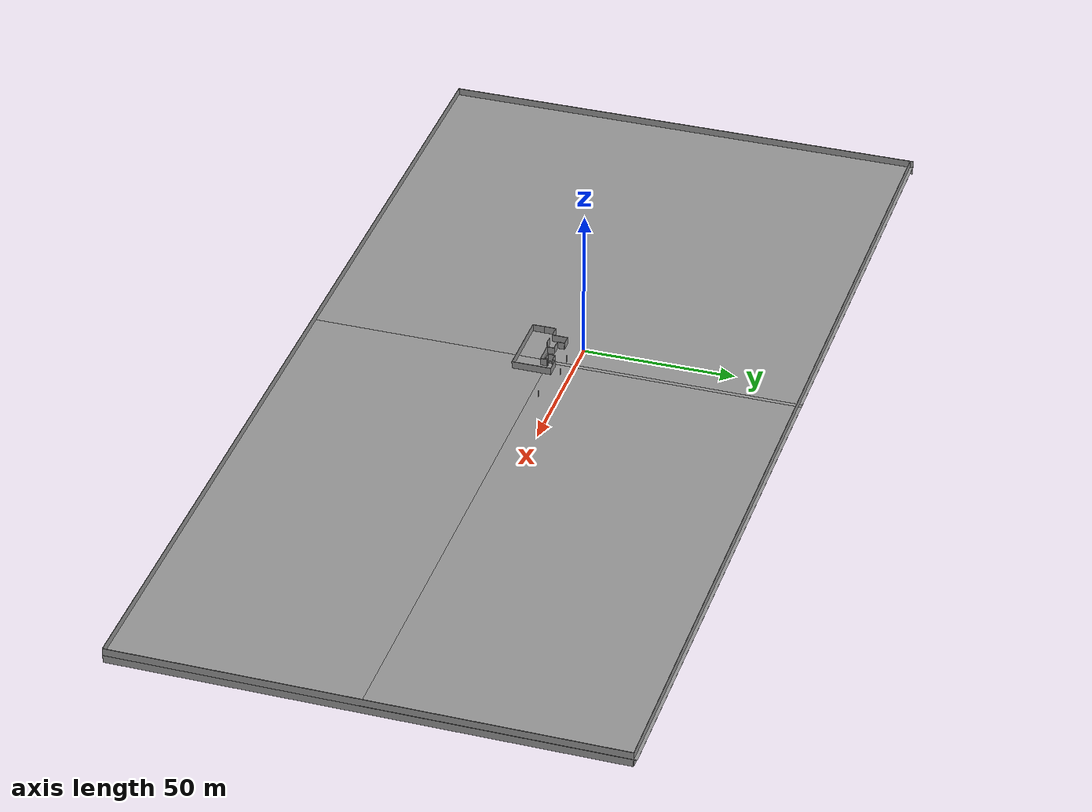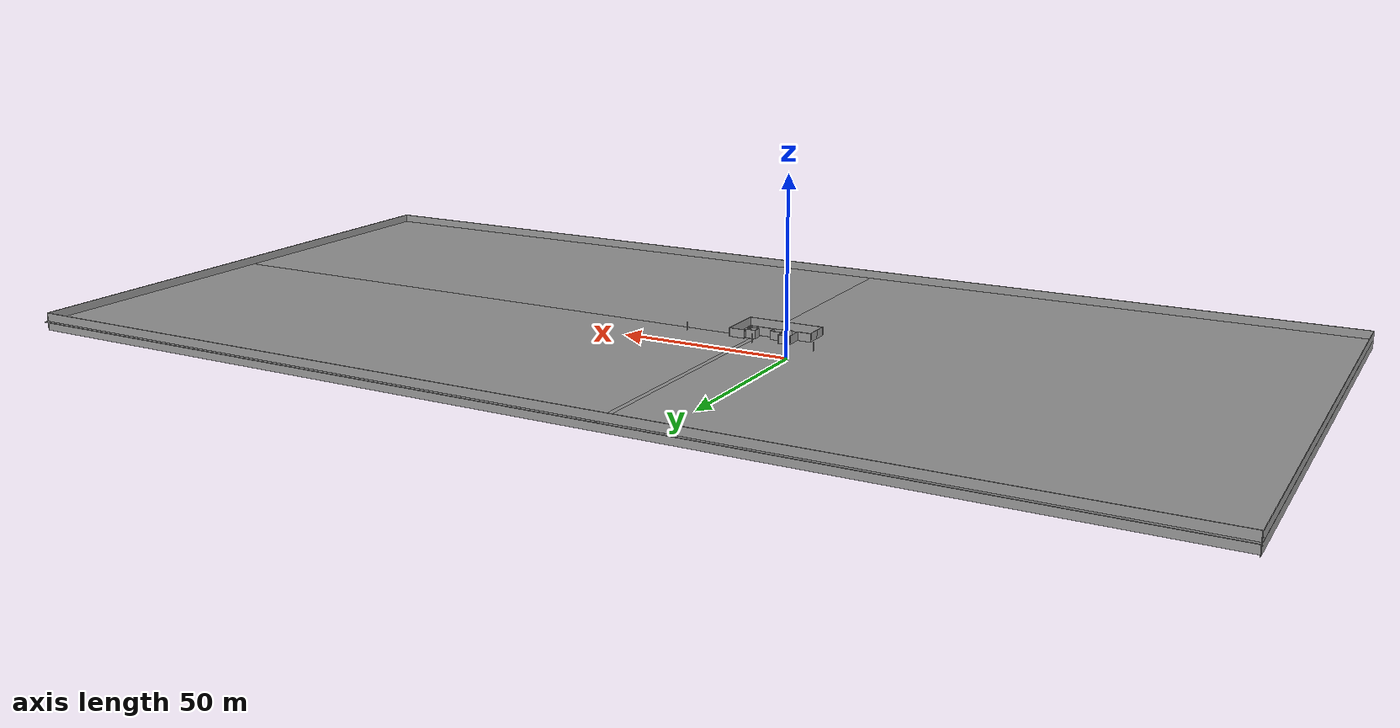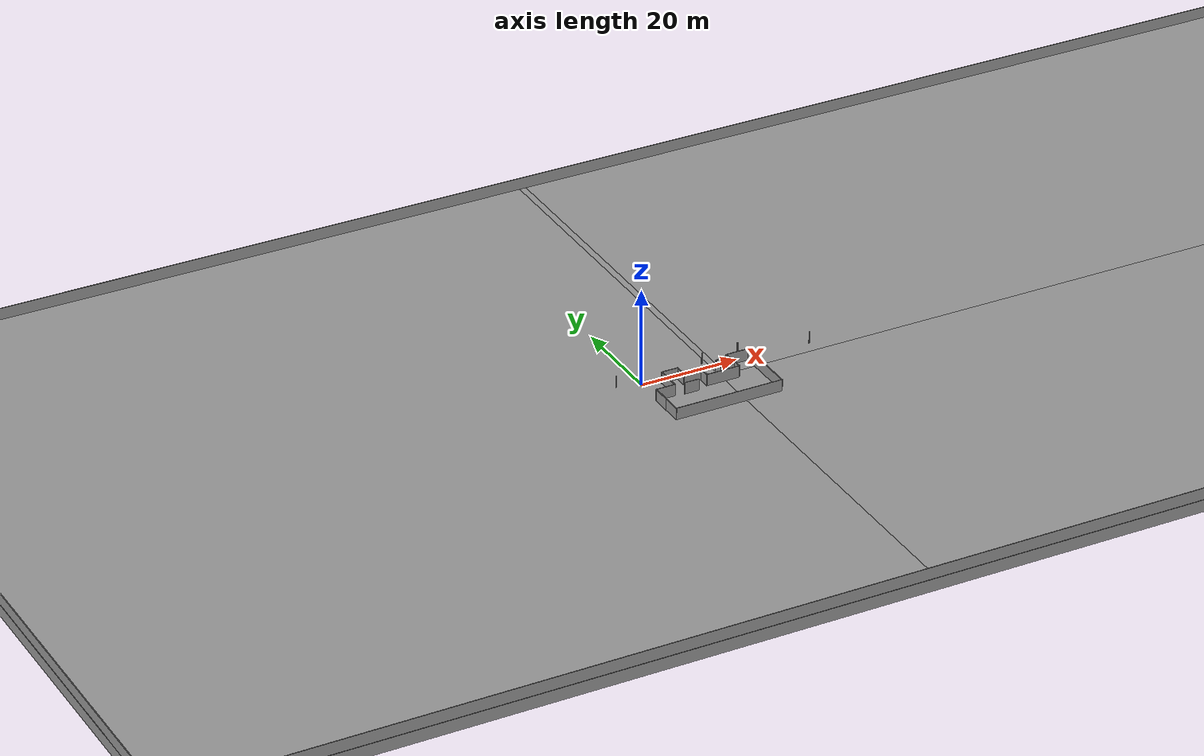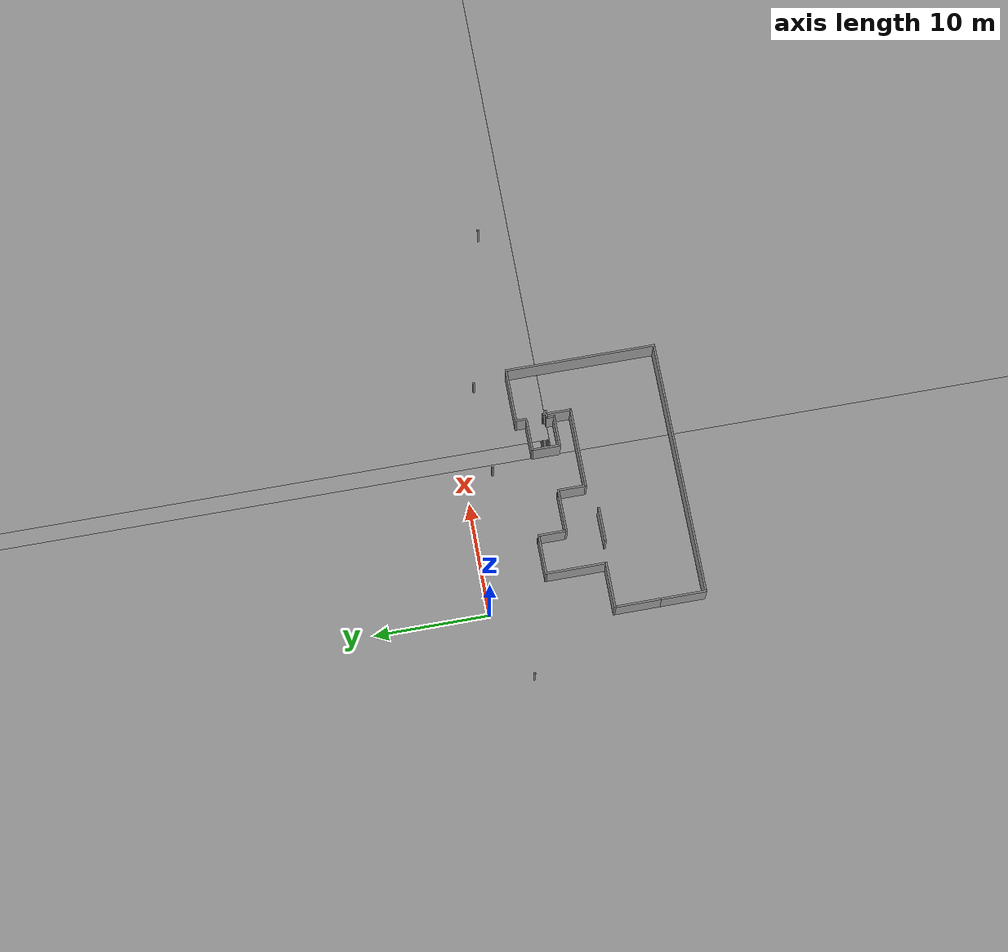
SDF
<?xml version='1.0'?>
<sdf version='1.4'>
  <model name='gdc'>
    <pose>30.4954 -5.57665 0 0 -0 0</pose>
    <link name='Floor_2'>
      <pose>-4e-06 2e-06 2.5 0 -0 0</pose>
      <visual name='Floor_2_Visual_0'>
        <pose>-91.9982 0 0.05 0 -0 0</pose>
        <geometry>
          <box>
            <size>147.754 161.75 0.1</size>
          </box>
        </geometry>
        <material>
          <script>
            <uri>file://media/materials/scripts/gazebo.material</uri>
            <name>Gazebo/Grey</name>
          </script>
          <ambient>1 1 1 1</ambient>
        </material>
      </visual>
      <collision name='Floor_2_Collision_0'>
        <geometry>
          <box>
            <size>147.754 161.75 0.1</size>
          </box>
        </geometry>
        <pose>-91.9982 0 0.05 0 -0 0</pose>
      </collision>
      <visual name='Floor_2_Visual_1'>
        <pose>73.8768 -41.4649 0.05 0 -0 0</pose>
        <geometry>
          <box>
            <size>183.996 78.8202 0.1</size>
          </box>
        </geometry>
        <material>
          <script>
            <uri>file://media/materials/scripts/gazebo.material</uri>
            <name>Gazebo/Grey</name>
          </script>
          <ambient>1 1 1 1</ambient>
        </material>
      </visual>
      <collision name='Floor_2_Collision_1'>
        <geometry>
          <box>
            <size>183.996 78.8202 0.1</size>
          </box>
        </geometry>
        <pose>73.8768 -41.4649 0.05 0 -0 0</pose>
      </collision>
      <visual name='Floor_2_Visual_2'>
        <pose>74.5746 39.4101 0.05 0 -0 0</pose>
        <geometry>
          <box>
            <size>182.601 82.9298 0.1</size>
          </box>
        </geometry>
        <material>
          <script>
            <uri>file://media/materials/scripts/gazebo.material</uri>
            <name>Gazebo/Grey</name>
          </script>
          <ambient>1 1 1 1</ambient>
        </material>
      </visual>
      <collision name='Floor_2_Collision_2'>
        <geometry>
          <box>
            <size>182.601 82.9298 0.1</size>
          </box>
        </geometry>
        <pose>74.5746 39.4101 0.05 0 -0 0</pose>
      </collision>
      <visual name='Floor_2_Visual_3'>
        <pose>-17.4236 39.7971 0.05 0 -0 0</pose>
        <geometry>
          <box>
            <size>1.39565 82.1558 0.1</size>
          </box>
        </geometry>
        <material>
          <script>
            <uri>file://media/materials/scripts/gazebo.material</uri>
            <name>Gazebo/Grey</name>
          </script>
          <ambient>1 1 1 1</ambient>
        </material>
      </visual>
      <collision name='Floor_2_Collision_3'>
        <geometry>
          <box>
            <size>1.39565 82.1558 0.1</size>
          </box>
        </geometry>
        <pose>-17.4236 39.7971 0.05 0 -0 0</pose>
      </collision>
    </link>
    <link name='Stairs_2'>
      <visual name='Stairs_2_Visual_0'>
        <pose>-18.0749 -1.6678 0.083333 0 -0 1.5708</pose>
        <geometry>
          <box>
            <size>0.773913 0.093043 0.166667</size>
          </box>
        </geometry>
        <material>
          <script>
            <uri>file://media/materials/scripts/gazebo.material</uri>
            <name>Gazebo/Grey</name>
          </script>
          <ambient>1 1 1 1</ambient>
        </material>
      </visual>
      <collision name='Stairs_2_Collision_0'>
        <geometry>
          <box>
            <size>0.773913 0.093043 0.166667</size>
          </box>
        </geometry>
        <pose>-18.0749 -1.6678 0.083333 0 -0 1.5708</pose>
      </collision>
      <visual name='Stairs_2_Visual_1'>
        <pose>-17.9819 -1.6678 0.25 0 -0 1.5708</pose>
        <geometry>
          <box>
            <size>0.773913 0.093043 0.166667</size>
          </box>
        </geometry>
        <material>
          <script>
            <uri>file://media/materials/scripts/gazebo.material</uri>
            <name>Gazebo/Grey</name>
          </script>
          <ambient>1 1 1 1</ambient>
        </material>
      </visual>
      <collision name='Stairs_2_Collision_1'>
        <geometry>
          <box>
            <size>0.773913 0.093043 0.166667</size>
          </box>
        </geometry>
        <pose>-17.9819 -1.6678 0.25 0 -0 1.5708</pose>
      </collision>
      <visual name='Stairs_2_Visual_2'>
        <pose>-17.8888 -1.6678 0.416667 0 -0 1.5708</pose>
        <geometry>
          <box>
            <size>0.773913 0.093043 0.166667</size>
          </box>
        </geometry>
        <material>
          <script>
            <uri>file://media/materials/scripts/gazebo.material</uri>
            <name>Gazebo/Grey</name>
          </script>
          <ambient>1 1 1 1</ambient>
        </material>
      </visual>
      <collision name='Stairs_2_Collision_2'>
        <geometry>
          <box>
            <size>0.773913 0.093043 0.166667</size>
          </box>
        </geometry>
        <pose>-17.8888 -1.6678 0.416667 0 -0 1.5708</pose>
      </collision>
      <visual name='Stairs_2_Visual_3'>
        <pose>-17.7958 -1.6678 0.583333 0 -0 1.5708</pose>
        <geometry>
          <box>
            <size>0.773913 0.093043 0.166667</size>
          </box>
        </geometry>
        <material>
          <script>
            <uri>file://media/materials/scripts/gazebo.material</uri>
            <name>Gazebo/Grey</name>
          </script>
          <ambient>1 1 1 1</ambient>
        </material>
      </visual>
      <collision name='Stairs_2_Collision_3'>
        <geometry>
          <box>
            <size>0.773913 0.093043 0.166667</size>
          </box>
        </geometry>
        <pose>-17.7958 -1.6678 0.583333 0 -0 1.5708</pose>
      </collision>
      <visual name='Stairs_2_Visual_4'>
        <pose>-17.7027 -1.6678 0.75 0 -0 1.5708</pose>
        <geometry>
          <box>
            <size>0.773913 0.093043 0.166667</size>
          </box>
        </geometry>
        <material>
          <script>
            <uri>file://media/materials/scripts/gazebo.material</uri>
            <name>Gazebo/Grey</name>
          </script>
          <ambient>1 1 1 1</ambient>
        </material>
      </visual>
      <collision name='Stairs_2_Collision_4'>
        <geometry>
          <box>
            <size>0.773913 0.093043 0.166667</size>
          </box>
        </geometry>
        <pose>-17.7027 -1.6678 0.75 0 -0 1.5708</pose>
      </collision>
      <visual name='Stairs_2_Visual_5'>
        <pose>-17.6097 -1.6678 0.916667 0 -0 1.5708</pose>
        <geometry>
          <box>
            <size>0.773913 0.093043 0.166667</size>
          </box>
        </geometry>
        <material>
          <script>
            <uri>file://media/materials/scripts/gazebo.material</uri>
            <name>Gazebo/Grey</name>
          </script>
          <ambient>1 1 1 1</ambient>
        </material>
      </visual>
      <collision name='Stairs_2_Collision_5'>
        <geometry>
          <box>
            <size>0.773913 0.093043 0.166667</size>
          </box>
        </geometry>
        <pose>-17.6097 -1.6678 0.916667 0 -0 1.5708</pose>
      </collision>
      <visual name='Stairs_2_Visual_6'>
        <pose>-17.5166 -1.6678 1.08333 0 -0 1.5708</pose>
        <geometry>
          <box>
            <size>0.773913 0.093043 0.166667</size>
          </box>
        </geometry>
        <material>
          <script>
            <uri>file://media/materials/scripts/gazebo.material</uri>
            <name>Gazebo/Grey</name>
          </script>
          <ambient>1 1 1 1</ambient>
        </material>
      </visual>
      <collision name='Stairs_2_Collision_6'>
        <geometry>
          <box>
            <size>0.773913 0.093043 0.166667</size>
          </box>
        </geometry>
        <pose>-17.5166 -1.6678 1.08333 0 -0 1.5708</pose>
      </collision>
      <visual name='Stairs_2_Visual_7'>
        <pose>-17.4236 -1.6678 1.25 0 -0 1.5708</pose>
        <geometry>
          <box>
            <size>0.773913 0.093043 0.166667</size>
          </box>
        </geometry>
        <material>
          <script>
            <uri>file://media/materials/scripts/gazebo.material</uri>
            <name>Gazebo/Grey</name>
          </script>
          <ambient>1 1 1 1</ambient>
        </material>
      </visual>
      <collision name='Stairs_2_Collision_7'>
        <geometry>
          <box>
            <size>0.773913 0.093043 0.166667</size>
          </box>
        </geometry>
        <pose>-17.4236 -1.6678 1.25 0 -0 1.5708</pose>
      </collision>
      <visual name='Stairs_2_Visual_8'>
        <pose>-17.3305 -1.6678 1.41667 0 -0 1.5708</pose>
        <geometry>
          <box>
            <size>0.773913 0.093043 0.166667</size>
          </box>
        </geometry>
        <material>
          <script>
            <uri>file://media/materials/scripts/gazebo.material</uri>
            <name>Gazebo/Grey</name>
          </script>
          <ambient>1 1 1 1</ambient>
        </material>
      </visual>
      <collision name='Stairs_2_Collision_8'>
        <geometry>
          <box>
            <size>0.773913 0.093043 0.166667</size>
          </box>
        </geometry>
        <pose>-17.3305 -1.6678 1.41667 0 -0 1.5708</pose>
      </collision>
      <visual name='Stairs_2_Visual_9'>
        <pose>-17.2375 -1.6678 1.58333 0 -0 1.5708</pose>
        <geometry>
          <box>
            <size>0.773913 0.093043 0.166667</size>
          </box>
        </geometry>
        <material>
          <script>
            <uri>file://media/materials/scripts/gazebo.material</uri>
            <name>Gazebo/Grey</name>
          </script>
          <ambient>1 1 1 1</ambient>
        </material>
      </visual>
      <collision name='Stairs_2_Collision_9'>
        <geometry>
          <box>
            <size>0.773913 0.093043 0.166667</size>
          </box>
        </geometry>
        <pose>-17.2375 -1.6678 1.58333 0 -0 1.5708</pose>
      </collision>
      <visual name='Stairs_2_Visual_10'>
        <pose>-17.1445 -1.6678 1.75 0 -0 1.5708</pose>
        <geometry>
          <box>
            <size>0.773913 0.093043 0.166667</size>
          </box>
        </geometry>
        <material>
          <script>
            <uri>file://media/materials/scripts/gazebo.material</uri>
            <name>Gazebo/Grey</name>
          </script>
          <ambient>1 1 1 1</ambient>
        </material>
      </visual>
      <collision name='Stairs_2_Collision_10'>
        <geometry>
          <box>
            <size>0.773913 0.093043 0.166667</size>
          </box>
        </geometry>
        <pose>-17.1445 -1.6678 1.75 0 -0 1.5708</pose>
      </collision>
      <visual name='Stairs_2_Visual_11'>
        <pose>-17.0514 -1.6678 1.91667 0 -0 1.5708</pose>
        <geometry>
          <box>
            <size>0.773913 0.093043 0.166667</size>
          </box>
        </geometry>
        <material>
          <script>
            <uri>file://media/materials/scripts/gazebo.material</uri>
            <name>Gazebo/Grey</name>
          </script>
          <ambient>1 1 1 1</ambient>
        </material>
      </visual>
      <collision name='Stairs_2_Collision_11'>
        <geometry>
          <box>
            <size>0.773913 0.093043 0.166667</size>
          </box>
        </geometry>
        <pose>-17.0514 -1.6678 1.91667 0 -0 1.5708</pose>
      </collision>
      <visual name='Stairs_2_Visual_12'>
        <pose>-16.9584 -1.6678 2.08333 0 -0 1.5708</pose>
        <geometry>
          <box>
            <size>0.773913 0.093043 0.166667</size>
          </box>
        </geometry>
        <material>
          <script>
            <uri>file://media/materials/scripts/gazebo.material</uri>
            <name>Gazebo/Grey</name>
          </script>
          <ambient>1 1 1 1</ambient>
        </material>
      </visual>
      <collision name='Stairs_2_Collision_12'>
        <geometry>
          <box>
            <size>0.773913 0.093043 0.166667</size>
          </box>
        </geometry>
        <pose>-16.9584 -1.6678 2.08333 0 -0 1.5708</pose>
      </collision>
      <visual name='Stairs_2_Visual_13'>
        <pose>-16.8653 -1.6678 2.25 0 -0 1.5708</pose>
        <geometry>
          <box>
            <size>0.773913 0.093043 0.166667</size>
          </box>
        </geometry>
        <material>
          <script>
            <uri>file://media/materials/scripts/gazebo.material</uri>
            <name>Gazebo/Grey</name>
          </script>
          <ambient>1 1 1 1</ambient>
        </material>
      </visual>
      <collision name='Stairs_2_Collision_13'>
        <geometry>
          <box>
            <size>0.773913 0.093043 0.166667</size>
          </box>
        </geometry>
        <pose>-16.8653 -1.6678 2.25 0 -0 1.5708</pose>
      </collision>
      <visual name='Stairs_2_Visual_14'>
        <pose>-16.7723 -1.6678 2.41667 0 -0 1.5708</pose>
        <geometry>
          <box>
            <size>0.773913 0.093043 0.166667</size>
          </box>
        </geometry>
        <material>
          <script>
            <uri>file://media/materials/scripts/gazebo.material</uri>
            <name>Gazebo/Grey</name>
          </script>
          <ambient>1 1 1 1</ambient>
        </material>
      </visual>
      <collision name='Stairs_2_Collision_14'>
        <geometry>
          <box>
            <size>0.773913 0.093043 0.166667</size>
          </box>
        </geometry>
        <pose>-16.7723 -1.6678 2.41667 0 -0 1.5708</pose>
      </collision>
    </link>
    <link name='Wall_1'>
      <collision name='Wall_1_Collision'>
        <geometry>
          <box>
            <size>6.25 0.15 2.5</size>
          </box>
        </geometry>
        <pose>0 0 1.25 0 -0 0</pose>
      </collision>
      <visual name='Wall_1_Visual'>
        <pose>0 0 1.25 0 -0 0</pose>
        <geometry>
          <box>
            <size>6.25 0.15 2.5</size>
          </box>
        </geometry>
        <material>
          <script>
            <uri>file://media/materials/scripts/gazebo.material</uri>
            <name>Gazebo/Grey</name>
          </script>
          <ambient>1 1 1 1</ambient>
        </material>
      </visual>
      <pose>-38.1221 15.6081 0 0 -0 0</pose>
    </link>
    <link name='Wall_10'>
      <collision name='Wall_10_Collision'>
        <geometry>
          <box>
            <size>0.25 0.15 2.5</size>
          </box>
        </geometry>
        <pose>0 0 1.25 0 -0 0</pose>
      </collision>
      <visual name='Wall_10_Visual'>
        <pose>0 0 1.25 0 -0 0</pose>
        <geometry>
          <box>
            <size>0.25 0.15 2.5</size>
          </box>
        </geometry>
        <material>
          <script>
            <uri>file://media/materials/scripts/gazebo.material</uri>
            <name>Gazebo/Grey</name>
          </script>
          <ambient>1 1 1 1</ambient>
        </material>
      </visual>
      <pose>-34.6041 8.84683 0 0 0 -2.35619</pose>
    </link>
    <link name='Wall_100'>
      <collision name='Wall_100_Collision'>
        <geometry>
          <box>
            <size>1.5 0.15 2.5</size>
          </box>
        </geometry>
        <pose>0 0 1.25 0 -0 0</pose>
      </collision>
      <visual name='Wall_100_Visual'>
        <pose>0 0 1.25 0 -0 0</pose>
        <geometry>
          <box>
            <size>1.5 0.15 2.5</size>
          </box>
        </geometry>
        <material>
          <script>
            <uri>file://media/materials/scripts/gazebo.material</uri>
            <name>Gazebo/Grey</name>
          </script>
          <ambient>1 1 1 1</ambient>
        </material>
      </visual>
      <pose>6.33961 10.4419 0 0 -0 0</pose>
    </link>
    <link name='Wall_101'>
      <collision name='Wall_101_Collision'>
        <geometry>
          <box>
            <size>1.75 0.15 2.5</size>
          </box>
        </geometry>
        <pose>0 0 1.25 0 -0 0</pose>
      </collision>
      <visual name='Wall_101_Visual'>
        <pose>0 0 1.25 0 -0 0</pose>
        <geometry>
          <box>
            <size>1.75 0.15 2.5</size>
          </box>
        </geometry>
        <material>
          <script>
            <uri>file://media/materials/scripts/gazebo.material</uri>
            <name>Gazebo/Grey</name>
          </script>
          <ambient>1 1 1 1</ambient>
        </material>
      </visual>
      <pose>7.01461 9.64185 0 0 0 -1.5708</pose>
    </link>
    <link name='Wall_102'>
      <collision name='Wall_102_Collision'>
        <geometry>
          <box>
            <size>0.5 0.15 2.5</size>
          </box>
        </geometry>
        <pose>0 0 1.25 0 -0 0</pose>
      </collision>
      <visual name='Wall_102_Visual'>
        <pose>0 0 1.25 0 -0 0</pose>
        <geometry>
          <box>
            <size>0.5 0.15 2.5</size>
          </box>
        </geometry>
        <material>
          <script>
            <uri>file://media/materials/scripts/gazebo.material</uri>
            <name>Gazebo/Grey</name>
          </script>
          <ambient>1 1 1 1</ambient>
        </material>
      </visual>
      <pose>6.83961 8.84186 0 0 -0 3.14159</pose>
    </link>
    <link name='Wall_103'>
      <collision name='Wall_103_Collision'>
        <geometry>
          <box>
            <size>0.5 0.15 2.5</size>
          </box>
        </geometry>
        <pose>0 0 1.25 0 -0 0</pose>
      </collision>
      <visual name='Wall_103_Visual'>
        <pose>0 0 1.25 0 -0 0</pose>
        <geometry>
          <box>
            <size>0.5 0.15 2.5</size>
          </box>
        </geometry>
        <material>
          <script>
            <uri>file://media/materials/scripts/gazebo.material</uri>
            <name>Gazebo/Grey</name>
          </script>
          <ambient>1 1 1 1</ambient>
        </material>
      </visual>
      <pose>6.48961 8.84186 0 0 -0 3.14159</pose>
    </link>
    <link name='Wall_104'>
      <collision name='Wall_104_Collision'>
        <geometry>
          <box>
            <size>7.25 0.15 2.5</size>
          </box>
        </geometry>
        <pose>0 0 1.25 0 -0 0</pose>
      </collision>
      <visual name='Wall_104_Visual'>
        <pose>0 0 1.25 0 -0 0</pose>
        <geometry>
          <box>
            <size>7.25 0.15 2.5</size>
          </box>
        </geometry>
        <material>
          <script>
            <uri>file://media/materials/scripts/gazebo.material</uri>
            <name>Gazebo/Grey</name>
          </script>
          <ambient>1 1 1 1</ambient>
        </material>
      </visual>
      <pose>6.31461 5.29185 0 0 0 -1.5708</pose>
    </link>
    <link name='Wall_105'>
      <collision name='Wall_105_Collision'>
        <geometry>
          <box>
            <size>0.25 0.15 2.5</size>
          </box>
        </geometry>
        <pose>0 0 1.25 0 -0 0</pose>
      </collision>
      <visual name='Wall_105_Visual'>
        <pose>0 0 1.25 0 -0 0</pose>
        <geometry>
          <box>
            <size>0.25 0.15 2.5</size>
          </box>
        </geometry>
        <material>
          <script>
            <uri>file://media/materials/scripts/gazebo.material</uri>
            <name>Gazebo/Grey</name>
          </script>
          <ambient>1 1 1 1</ambient>
        </material>
      </visual>
      <pose>6.31461 1.69186 0 0 0 -1.5708</pose>
    </link>
    <link name='Wall_106'>
      <collision name='Wall_106_Collision'>
        <geometry>
          <box>
            <size>2.5 0.15 2.5</size>
          </box>
        </geometry>
        <pose>0 0 1.25 0 -0 0</pose>
      </collision>
      <visual name='Wall_106_Visual'>
        <pose>0 0 1.25 0 -0 0</pose>
        <geometry>
          <box>
            <size>2.5 0.15 2.5</size>
          </box>
        </geometry>
        <material>
          <script>
            <uri>file://media/materials/scripts/gazebo.material</uri>
            <name>Gazebo/Grey</name>
          </script>
          <ambient>1 1 1 1</ambient>
        </material>
      </visual>
      <pose>5.13961 1.64186 0 0 -0 3.14159</pose>
    </link>
    <link name='Wall_107'>
      <collision name='Wall_107_Collision'>
        <geometry>
          <box>
            <size>1 0.15 2.5</size>
          </box>
        </geometry>
        <pose>0 0 1.25 0 -0 0</pose>
      </collision>
      <visual name='Wall_107_Visual'>
        <pose>0 0 1.25 0 -0 0</pose>
        <geometry>
          <box>
            <size>1 0.15 2.5</size>
          </box>
        </geometry>
        <material>
          <script>
            <uri>file://media/materials/scripts/gazebo.material</uri>
            <name>Gazebo/Grey</name>
          </script>
          <ambient>1 1 1 1</ambient>
        </material>
      </visual>
      <pose>3.96461 1.21686 0 0 0 -1.5708</pose>
    </link>
    <link name='Wall_108'>
      <collision name='Wall_108_Collision'>
        <geometry>
          <box>
            <size>0.25 0.15 2.5</size>
          </box>
        </geometry>
        <pose>0 0 1.25 0 -0 0</pose>
      </collision>
      <visual name='Wall_108_Visual'>
        <pose>0 0 1.25 0 -0 0</pose>
        <geometry>
          <box>
            <size>0.25 0.15 2.5</size>
          </box>
        </geometry>
        <material>
          <script>
            <uri>file://media/materials/scripts/gazebo.material</uri>
            <name>Gazebo/Grey</name>
          </script>
          <ambient>1 1 1 1</ambient>
        </material>
      </visual>
      <pose>3.97755 0.743558 0 0 0 -1.309</pose>
    </link>
    <link name='Wall_109'>
      <collision name='Wall_109_Collision'>
        <geometry>
          <box>
            <size>1.75 0.15 2.5</size>
          </box>
        </geometry>
        <pose>0 0 1.25 0 -0 0</pose>
      </collision>
      <visual name='Wall_109_Visual'>
        <pose>0 0 1.25 0 -0 0</pose>
        <geometry>
          <box>
            <size>1.75 0.15 2.5</size>
          </box>
        </geometry>
        <material>
          <script>
            <uri>file://media/materials/scripts/gazebo.material</uri>
            <name>Gazebo/Grey</name>
          </script>
          <ambient>1 1 1 1</ambient>
        </material>
      </visual>
      <pose>3.19049 0.695262 0 0 -0 3.14159</pose>
    </link>
    <link name='Wall_11'>
      <collision name='Wall_11_Collision'>
        <geometry>
          <box>
            <size>0.25 0.15 2.5</size>
          </box>
        </geometry>
        <pose>0 0 1.25 0 -0 0</pose>
      </collision>
      <visual name='Wall_11_Visual'>
        <pose>0 0 1.25 0 -0 0</pose>
        <geometry>
          <box>
            <size>0.25 0.15 2.5</size>
          </box>
        </geometry>
        <material>
          <script>
            <uri>file://media/materials/scripts/gazebo.material</uri>
            <name>Gazebo/Grey</name>
          </script>
          <ambient>1 1 1 1</ambient>
        </material>
      </visual>
      <pose>-34.6748 8.77612 0 0 0 -2.35619</pose>
    </link>
    <link name='Wall_110'>
      <collision name='Wall_110_Collision'>
        <geometry>
          <box>
            <size>0.15 0.15 2.5</size>
          </box>
        </geometry>
        <pose>0 0 1.25 0 -0 0</pose>
      </collision>
      <visual name='Wall_110_Visual'>
        <pose>0 0 1.25 0 -0 0</pose>
        <geometry>
          <box>
            <size>0.15 0.15 2.5</size>
          </box>
        </geometry>
        <material>
          <script>
            <uri>file://media/materials/scripts/gazebo.material</uri>
            <name>Gazebo/Grey</name>
          </script>
          <ambient>1 1 1 1</ambient>
        </material>
      </visual>
      <pose>2.3905 0.695262 0 0 -0 0</pose>
    </link>
    <link name='Wall_111'>
      <collision name='Wall_111_Collision'>
        <geometry>
          <box>
            <size>1 0.15 2.5</size>
          </box>
        </geometry>
        <pose>0 0 1.25 0 -0 0</pose>
      </collision>
      <visual name='Wall_111_Visual'>
        <pose>0 0 1.25 0 -0 0</pose>
        <geometry>
          <box>
            <size>1 0.15 2.5</size>
          </box>
        </geometry>
        <material>
          <script>
            <uri>file://media/materials/scripts/gazebo.material</uri>
            <name>Gazebo/Grey</name>
          </script>
          <ambient>1 1 1 1</ambient>
        </material>
      </visual>
      <pose>2.40372 1.12026 0 0 -0 1.53969</pose>
    </link>
    <link name='Wall_114'>
      <collision name='Wall_114_Collision'>
        <geometry>
          <box>
            <size>0.25 0.15 2.5</size>
          </box>
        </geometry>
        <pose>0 0 1.25 0 -0 0</pose>
      </collision>
      <visual name='Wall_114_Visual'>
        <pose>0 0 1.25 0 -0 0</pose>
        <geometry>
          <box>
            <size>0.25 0.15 2.5</size>
          </box>
        </geometry>
        <material>
          <script>
            <uri>file://media/materials/scripts/gazebo.material</uri>
            <name>Gazebo/Grey</name>
          </script>
          <ambient>1 1 1 1</ambient>
        </material>
      </visual>
      <pose>2.41694 1.59526 0 0 -0 1.5708</pose>
    </link>
    <link name='Wall_115'>
      <collision name='Wall_115_Collision'>
        <geometry>
          <box>
            <size>8.25 0.15 2.5</size>
          </box>
        </geometry>
        <pose>0 0 1.25 0 -0 0</pose>
      </collision>
      <visual name='Wall_115_Visual'>
        <pose>0 0 1.25 0 -0 0</pose>
        <geometry>
          <box>
            <size>8.25 0.15 2.5</size>
          </box>
        </geometry>
        <material>
          <script>
            <uri>file://media/materials/scripts/gazebo.material</uri>
            <name>Gazebo/Grey</name>
          </script>
          <ambient>1 1 1 1</ambient>
        </material>
      </visual>
      <pose>-1.63306 1.64526 0 0 -0 3.14159</pose>
    </link>
    <link name='Wall_116'>
      <collision name='Wall_116_Collision'>
        <geometry>
          <box>
            <size>0.25 0.15 2.5</size>
          </box>
        </geometry>
        <pose>0 0 1.25 0 -0 0</pose>
      </collision>
      <visual name='Wall_116_Visual'>
        <pose>0 0 1.25 0 -0 0</pose>
        <geometry>
          <box>
            <size>0.25 0.15 2.5</size>
          </box>
        </geometry>
        <material>
          <script>
            <uri>file://media/materials/scripts/gazebo.material</uri>
            <name>Gazebo/Grey</name>
          </script>
          <ambient>1 1 1 1</ambient>
        </material>
      </visual>
      <pose>-5.73306 1.64526 0 0 -0 3.14159</pose>
    </link>
    <link name='Wall_117'>
      <collision name='Wall_117_Collision'>
        <geometry>
          <box>
            <size>0.25 0.15 2.5</size>
          </box>
        </geometry>
        <pose>0 0 1.25 0 -0 0</pose>
      </collision>
      <visual name='Wall_117_Visual'>
        <pose>0 0 1.25 0 -0 0</pose>
        <geometry>
          <box>
            <size>0.25 0.15 2.5</size>
          </box>
        </geometry>
        <material>
          <script>
            <uri>file://media/materials/scripts/gazebo.material</uri>
            <name>Gazebo/Grey</name>
          </script>
          <ambient>1 1 1 1</ambient>
        </material>
      </visual>
      <pose>-5.83305 1.64526 0 0 -0 3.14159</pose>
    </link>
    <link name='Wall_118'>
      <collision name='Wall_118_Collision'>
        <geometry>
          <box>
            <size>1.75 0.15 2.5</size>
          </box>
        </geometry>
        <pose>0 0 1.25 0 -0 0</pose>
      </collision>
      <visual name='Wall_118_Visual'>
        <pose>0 0 1.25 0 -0 0</pose>
        <geometry>
          <box>
            <size>1.75 0.15 2.5</size>
          </box>
        </geometry>
        <material>
          <script>
            <uri>file://media/materials/scripts/gazebo.material</uri>
            <name>Gazebo/Grey</name>
          </script>
          <ambient>1 1 1 1</ambient>
        </material>
      </visual>
      <pose>-5.88306 0.845263 0 0 0 -1.5708</pose>
    </link>
    <link name='Wall_119'>
      <collision name='Wall_119_Collision'>
        <geometry>
          <box>
            <size>3 0.15 2.5</size>
          </box>
        </geometry>
        <pose>0 0 1.25 0 -0 0</pose>
      </collision>
      <visual name='Wall_119_Visual'>
        <pose>0 0 1.25 0 -0 0</pose>
        <geometry>
          <box>
            <size>3 0.15 2.5</size>
          </box>
        </geometry>
        <material>
          <script>
            <uri>file://media/materials/scripts/gazebo.material</uri>
            <name>Gazebo/Grey</name>
          </script>
          <ambient>1 1 1 1</ambient>
        </material>
      </visual>
      <pose>-7.30806 0.045262 0 0 -0 3.14159</pose>
    </link>
    <link name='Wall_120'>
      <collision name='Wall_120_Collision'>
        <geometry>
          <box>
            <size>1.75 0.15 2.5</size>
          </box>
        </geometry>
        <pose>0 0 1.25 0 -0 0</pose>
      </collision>
      <visual name='Wall_120_Visual'>
        <pose>0 0 1.25 0 -0 0</pose>
        <geometry>
          <box>
            <size>1.75 0.15 2.5</size>
          </box>
        </geometry>
        <material>
          <script>
            <uri>file://media/materials/scripts/gazebo.material</uri>
            <name>Gazebo/Grey</name>
          </script>
          <ambient>1 1 1 1</ambient>
        </material>
      </visual>
      <pose>-8.73306 0.845263 0 0 -0 1.5708</pose>
    </link>
    <link name='Wall_121'>
      <collision name='Wall_121_Collision'>
        <geometry>
          <box>
            <size>2.75 0.15 2.5</size>
          </box>
        </geometry>
        <pose>0 0 1.25 0 -0 0</pose>
      </collision>
      <visual name='Wall_121_Visual'>
        <pose>0 0 1.25 0 -0 0</pose>
        <geometry>
          <box>
            <size>2.75 0.15 2.5</size>
          </box>
        </geometry>
        <material>
          <script>
            <uri>file://media/materials/scripts/gazebo.material</uri>
            <name>Gazebo/Grey</name>
          </script>
          <ambient>1 1 1 1</ambient>
        </material>
      </visual>
      <pose>-10.0331 1.64526 0 0 -0 3.14159</pose>
    </link>
    <link name='Wall_123'>
      <collision name='Wall_123_Collision'>
        <geometry>
          <box>
            <size>4.75 0.15 2.5</size>
          </box>
        </geometry>
        <pose>0 0 1.25 0 -0 0</pose>
      </collision>
      <visual name='Wall_123_Visual'>
        <pose>0 0 1.25 0 -0 0</pose>
        <geometry>
          <box>
            <size>4.75 0.15 2.5</size>
          </box>
        </geometry>
        <material>
          <script>
            <uri>file://media/materials/scripts/gazebo.material</uri>
            <name>Gazebo/Grey</name>
          </script>
          <ambient>1 1 1 1</ambient>
        </material>
      </visual>
      <pose>-11.3331 -0.654737 0 0 0 -1.5708</pose>
    </link>
    <link name='Wall_124'>
      <collision name='Wall_124_Collision'>
        <geometry>
          <box>
            <size>0.75 0.15 2.5</size>
          </box>
        </geometry>
        <pose>0 0 1.25 0 -0 0</pose>
      </collision>
      <visual name='Wall_124_Visual'>
        <pose>0 0 1.25 0 -0 0</pose>
        <geometry>
          <box>
            <size>0.75 0.15 2.5</size>
          </box>
        </geometry>
        <material>
          <script>
            <uri>file://media/materials/scripts/gazebo.material</uri>
            <name>Gazebo/Grey</name>
          </script>
          <ambient>1 1 1 1</ambient>
        </material>
      </visual>
      <pose>-11.4107 -3.24451 0 0 0 -1.8326</pose>
    </link>
    <link name='Wall_125'>
      <collision name='Wall_125_Collision'>
        <geometry>
          <box>
            <size>3.5 0.15 2.5</size>
          </box>
        </geometry>
        <pose>0 0 1.25 0 -0 0</pose>
      </collision>
      <visual name='Wall_125_Visual'>
        <pose>0 0 1.25 0 -0 0</pose>
        <geometry>
          <box>
            <size>3.5 0.15 2.5</size>
          </box>
        </geometry>
        <material>
          <script>
            <uri>file://media/materials/scripts/gazebo.material</uri>
            <name>Gazebo/Grey</name>
          </script>
          <ambient>1 1 1 1</ambient>
        </material>
      </visual>
      <pose>-13.1633 -3.53429 0 0 -0 3.14159</pose>
    </link>
    <link name='Wall_126'>
      <collision name='Wall_126_Collision'>
        <geometry>
          <box>
            <size>0.75 0.15 2.5</size>
          </box>
        </geometry>
        <pose>0 0 1.25 0 -0 0</pose>
      </collision>
      <visual name='Wall_126_Visual'>
        <pose>0 0 1.25 0 -0 0</pose>
        <geometry>
          <box>
            <size>0.75 0.15 2.5</size>
          </box>
        </geometry>
        <material>
          <script>
            <uri>file://media/materials/scripts/gazebo.material</uri>
            <name>Gazebo/Grey</name>
          </script>
          <ambient>1 1 1 1</ambient>
        </material>
      </visual>
      <pose>-14.9883 -3.27449 0 0 -0 2.0944</pose>
    </link>
    <link name='Wall_127'>
      <collision name='Wall_127_Collision'>
        <geometry>
          <box>
            <size>1 0.15 2.5</size>
          </box>
        </geometry>
        <pose>0 0 1.25 0 -0 0</pose>
      </collision>
      <visual name='Wall_127_Visual'>
        <pose>0 0 1.25 0 -0 0</pose>
        <geometry>
          <box>
            <size>1 0.15 2.5</size>
          </box>
        </geometry>
        <material>
          <script>
            <uri>file://media/materials/scripts/gazebo.material</uri>
            <name>Gazebo/Grey</name>
          </script>
          <ambient>1 1 1 1</ambient>
        </material>
      </visual>
      <pose>-15.1383 -2.58968 0 0 -0 1.5708</pose>
    </link>
    <link name='Wall_128'>
      <collision name='Wall_128_Collision'>
        <geometry>
          <box>
            <size>0.5 0.15 2.5</size>
          </box>
        </geometry>
        <pose>0 0 1.25 0 -0 0</pose>
      </collision>
      <visual name='Wall_128_Visual'>
        <pose>0 0 1.25 0 -0 0</pose>
        <geometry>
          <box>
            <size>0.5 0.15 2.5</size>
          </box>
        </geometry>
        <material>
          <script>
            <uri>file://media/materials/scripts/gazebo.material</uri>
            <name>Gazebo/Grey</name>
          </script>
          <ambient>1 1 1 1</ambient>
        </material>
      </visual>
      <pose>-15.3133 -2.16468 0 0 -0 3.14159</pose>
    </link>
    <link name='Wall_129'>
      <collision name='Wall_129_Collision'>
        <geometry>
          <box>
            <size>0.25 0.15 2.5</size>
          </box>
        </geometry>
        <pose>0 0 1.25 0 -0 0</pose>
      </collision>
      <visual name='Wall_129_Visual'>
        <pose>0 0 1.25 0 -0 0</pose>
        <geometry>
          <box>
            <size>0.25 0.15 2.5</size>
          </box>
        </geometry>
        <material>
          <script>
            <uri>file://media/materials/scripts/gazebo.material</uri>
            <name>Gazebo/Grey</name>
          </script>
          <ambient>1 1 1 1</ambient>
        </material>
      </visual>
      <pose>-15.5383 -2.16468 0 0 -0 3.14159</pose>
    </link>
    <link name='Wall_130'>
      <collision name='Wall_130_Collision'>
        <geometry>
          <box>
            <size>0.5 0.15 2.5</size>
          </box>
        </geometry>
        <pose>0 0 1.25 0 -0 0</pose>
      </collision>
      <visual name='Wall_130_Visual'>
        <pose>0 0 1.25 0 -0 0</pose>
        <geometry>
          <box>
            <size>0.5 0.15 2.5</size>
          </box>
        </geometry>
        <material>
          <script>
            <uri>file://media/materials/scripts/gazebo.material</uri>
            <name>Gazebo/Grey</name>
          </script>
          <ambient>1 1 1 1</ambient>
        </material>
      </visual>
      <pose>-15.5883 -2.33968 0 0 0 -1.5708</pose>
    </link>
    <link name='Wall_131'>
      <collision name='Wall_131_Collision'>
        <geometry>
          <box>
            <size>0.25 0.15 2.5</size>
          </box>
        </geometry>
        <pose>0 0 1.25 0 -0 0</pose>
      </collision>
      <visual name='Wall_131_Visual'>
        <pose>0 0 1.25 0 -0 0</pose>
        <geometry>
          <box>
            <size>0.25 0.15 2.5</size>
          </box>
        </geometry>
        <material>
          <script>
            <uri>file://media/materials/scripts/gazebo.material</uri>
            <name>Gazebo/Grey</name>
          </script>
          <ambient>1 1 1 1</ambient>
        </material>
      </visual>
      <pose>-15.5883 -2.56468 0 0 0 -1.5708</pose>
    </link>
    <link name='Wall_132'>
      <collision name='Wall_132_Collision'>
        <geometry>
          <box>
            <size>3 0.15 2.5</size>
          </box>
        </geometry>
        <pose>0 0 1.25 0 -0 0</pose>
      </collision>
      <visual name='Wall_132_Visual'>
        <pose>0 0 1.25 0 -0 0</pose>
        <geometry>
          <box>
            <size>3 0.15 2.5</size>
          </box>
        </geometry>
        <material>
          <script>
            <uri>file://media/materials/scripts/gazebo.material</uri>
            <name>Gazebo/Grey</name>
          </script>
          <ambient>1 1 1 1</ambient>
        </material>
      </visual>
      <pose>-17.0133 -2.61468 0 0 -0 3.14159</pose>
    </link>
    <link name='Wall_133'>
      <collision name='Wall_133_Collision'>
        <geometry>
          <box>
            <size>2.5 0.15 2.5</size>
          </box>
        </geometry>
        <pose>0 0 1.25 0 -0 0</pose>
      </collision>
      <visual name='Wall_133_Visual'>
        <pose>0 0 1.25 0 -0 0</pose>
        <geometry>
          <box>
            <size>2.5 0.15 2.5</size>
          </box>
        </geometry>
        <material>
          <script>
            <uri>file://media/materials/scripts/gazebo.material</uri>
            <name>Gazebo/Grey</name>
          </script>
          <ambient>1 1 1 1</ambient>
        </material>
      </visual>
      <pose>-18.4383 -1.43968 0 0 -0 1.5708</pose>
    </link>
    <link name='Wall_134'>
      <collision name='Wall_134_Collision'>
        <geometry>
          <box>
            <size>0.25 0.15 2.5</size>
          </box>
        </geometry>
        <pose>0 0 1.25 0 -0 0</pose>
      </collision>
      <visual name='Wall_134_Visual'>
        <pose>0 0 1.25 0 -0 0</pose>
        <geometry>
          <box>
            <size>0.25 0.15 2.5</size>
          </box>
        </geometry>
        <material>
          <script>
            <uri>file://media/materials/scripts/gazebo.material</uri>
            <name>Gazebo/Grey</name>
          </script>
          <ambient>1 1 1 1</ambient>
        </material>
      </visual>
      <pose>-18.4383 -0.214678 0 0 -0 1.5708</pose>
    </link>
    <link name='Wall_135'>
      <collision name='Wall_135_Collision'>
        <geometry>
          <box>
            <size>3 0.15 2.5</size>
          </box>
        </geometry>
        <pose>0 0 1.25 0 -0 0</pose>
      </collision>
      <visual name='Wall_135_Visual'>
        <pose>0 0 1.25 0 -0 0</pose>
        <geometry>
          <box>
            <size>3 0.15 2.5</size>
          </box>
        </geometry>
        <material>
          <script>
            <uri>file://media/materials/scripts/gazebo.material</uri>
            <name>Gazebo/Grey</name>
          </script>
          <ambient>1 1 1 1</ambient>
        </material>
      </visual>
      <pose>-17.0133 -0.164678 0 0 -0 0</pose>
    </link>
    <link name='Wall_136'>
      <collision name='Wall_136_Collision'>
        <geometry>
          <box>
            <size>0.5 0.15 2.5</size>
          </box>
        </geometry>
        <pose>0 0 1.25 0 -0 0</pose>
      </collision>
      <visual name='Wall_136_Visual'>
        <pose>0 0 1.25 0 -0 0</pose>
        <geometry>
          <box>
            <size>0.5 0.15 2.5</size>
          </box>
        </geometry>
        <material>
          <script>
            <uri>file://media/materials/scripts/gazebo.material</uri>
            <name>Gazebo/Grey</name>
          </script>
          <ambient>1 1 1 1</ambient>
        </material>
      </visual>
      <pose>-15.5883 -0.339678 0 0 0 -1.5708</pose>
    </link>
    <link name='Wall_137'>
      <collision name='Wall_137_Collision'>
        <geometry>
          <box>
            <size>0.5 0.15 2.5</size>
          </box>
        </geometry>
        <pose>0 0 1.25 0 -0 0</pose>
      </collision>
      <visual name='Wall_137_Visual'>
        <pose>0 0 1.25 0 -0 0</pose>
        <geometry>
          <box>
            <size>0.5 0.15 2.5</size>
          </box>
        </geometry>
        <material>
          <script>
            <uri>file://media/materials/scripts/gazebo.material</uri>
            <name>Gazebo/Grey</name>
          </script>
          <ambient>1 1 1 1</ambient>
        </material>
      </visual>
      <pose>-15.4133 -0.514678 0 0 -0 0</pose>
    </link>
    <link name='Wall_138'>
      <collision name='Wall_138_Collision'>
        <geometry>
          <box>
            <size>0.25 0.15 2.5</size>
          </box>
        </geometry>
        <pose>0 0 1.25 0 -0 0</pose>
      </collision>
      <visual name='Wall_138_Visual'>
        <pose>0 0 1.25 0 -0 0</pose>
        <geometry>
          <box>
            <size>0.25 0.15 2.5</size>
          </box>
        </geometry>
        <material>
          <script>
            <uri>file://media/materials/scripts/gazebo.material</uri>
            <name>Gazebo/Grey</name>
          </script>
          <ambient>1 1 1 1</ambient>
        </material>
      </visual>
      <pose>-15.1883 -0.514678 0 0 -0 0</pose>
    </link>
    <link name='Wall_139'>
      <collision name='Wall_139_Collision'>
        <geometry>
          <box>
            <size>0.5 0.15 2.5</size>
          </box>
        </geometry>
        <pose>0 0 1.25 0 -0 0</pose>
      </collision>
      <visual name='Wall_139_Visual'>
        <pose>0 0 1.25 0 -0 0</pose>
        <geometry>
          <box>
            <size>0.5 0.15 2.5</size>
          </box>
        </geometry>
        <material>
          <script>
            <uri>file://media/materials/scripts/gazebo.material</uri>
            <name>Gazebo/Grey</name>
          </script>
          <ambient>1 1 1 1</ambient>
        </material>
      </visual>
      <pose>-15.1383 -0.339678 0 0 -0 1.5708</pose>
    </link>
    <link name='Wall_14'>
      <collision name='Wall_14_Collision'>
        <geometry>
          <box>
            <size>0.5 0.15 2.5</size>
          </box>
        </geometry>
        <pose>0 0 1.25 0 -0 0</pose>
      </collision>
      <visual name='Wall_14_Visual'>
        <pose>0 0 1.25 0 -0 0</pose>
        <geometry>
          <box>
            <size>0.5 0.15 2.5</size>
          </box>
        </geometry>
        <material>
          <script>
            <uri>file://media/materials/scripts/gazebo.material</uri>
            <name>Gazebo/Grey</name>
          </script>
          <ambient>1 1 1 1</ambient>
        </material>
      </visual>
      <pose>-34.6394 8.63647 0 0 0 -1.5708</pose>
    </link>
    <link name='Wall_140'>
      <collision name='Wall_140_Collision'>
        <geometry>
          <box>
            <size>0.75 0.15 2.5</size>
          </box>
        </geometry>
        <pose>0 0 1.25 0 -0 0</pose>
      </collision>
      <visual name='Wall_140_Visual'>
        <pose>0 0 1.25 0 -0 0</pose>
        <geometry>
          <box>
            <size>0.75 0.15 2.5</size>
          </box>
        </geometry>
        <material>
          <script>
            <uri>file://media/materials/scripts/gazebo.material</uri>
            <name>Gazebo/Grey</name>
          </script>
          <ambient>1 1 1 1</ambient>
        </material>
      </visual>
      <pose>-14.8383 -0.164678 0 0 -0 0</pose>
    </link>
    <link name='Wall_141'>
      <collision name='Wall_141_Collision'>
        <geometry>
          <box>
            <size>0.5 0.15 2.5</size>
          </box>
        </geometry>
        <pose>0 0 1.25 0 -0 0</pose>
      </collision>
      <visual name='Wall_141_Visual'>
        <pose>0 0 1.25 0 -0 0</pose>
        <geometry>
          <box>
            <size>0.5 0.15 2.5</size>
          </box>
        </geometry>
        <material>
          <script>
            <uri>file://media/materials/scripts/gazebo.material</uri>
            <name>Gazebo/Grey</name>
          </script>
          <ambient>1 1 1 1</ambient>
        </material>
      </visual>
      <pose>-14.5836 0.004359 0 0 -0 1.8326</pose>
    </link>
    <link name='Wall_142'>
      <collision name='Wall_142_Collision'>
        <geometry>
          <box>
            <size>0.5 0.15 2.5</size>
          </box>
        </geometry>
        <pose>0 0 1.25 0 -0 0</pose>
      </collision>
      <visual name='Wall_142_Visual'>
        <pose>0 0 1.25 0 -0 0</pose>
        <geometry>
          <box>
            <size>0.5 0.15 2.5</size>
          </box>
        </geometry>
        <material>
          <script>
            <uri>file://media/materials/scripts/gazebo.material</uri>
            <name>Gazebo/Grey</name>
          </script>
          <ambient>1 1 1 1</ambient>
        </material>
      </visual>
      <pose>-14.8039 0.173396 0 0 -0 3.14159</pose>
    </link>
    <link name='Wall_143'>
      <collision name='Wall_143_Collision'>
        <geometry>
          <box>
            <size>0.75 0.15 2.5</size>
          </box>
        </geometry>
        <pose>0 0 1.25 0 -0 0</pose>
      </collision>
      <visual name='Wall_143_Visual'>
        <pose>0 0 1.25 0 -0 0</pose>
        <geometry>
          <box>
            <size>0.75 0.15 2.5</size>
          </box>
        </geometry>
        <material>
          <script>
            <uri>file://media/materials/scripts/gazebo.material</uri>
            <name>Gazebo/Grey</name>
          </script>
          <ambient>1 1 1 1</ambient>
        </material>
      </visual>
      <pose>-14.9789 0.473396 0 0 -0 1.5708</pose>
    </link>
    <link name='Wall_144'>
      <collision name='Wall_144_Collision'>
        <geometry>
          <box>
            <size>0.5 0.15 2.5</size>
          </box>
        </geometry>
        <pose>0 0 1.25 0 -0 0</pose>
      </collision>
      <visual name='Wall_144_Visual'>
        <pose>0 0 1.25 0 -0 0</pose>
        <geometry>
          <box>
            <size>0.5 0.15 2.5</size>
          </box>
        </geometry>
        <material>
          <script>
            <uri>file://media/materials/scripts/gazebo.material</uri>
            <name>Gazebo/Grey</name>
          </script>
          <ambient>1 1 1 1</ambient>
        </material>
      </visual>
      <pose>-14.8039 0.773396 0 0 -0 0</pose>
    </link>
    <link name='Wall_145'>
      <collision name='Wall_145_Collision'>
        <geometry>
          <box>
            <size>1 0.15 2.5</size>
          </box>
        </geometry>
        <pose>0 0 1.25 0 -0 0</pose>
      </collision>
      <visual name='Wall_145_Visual'>
        <pose>0 0 1.25 0 -0 0</pose>
        <geometry>
          <box>
            <size>1 0.15 2.5</size>
          </box>
        </geometry>
        <material>
          <script>
            <uri>file://media/materials/scripts/gazebo.material</uri>
            <name>Gazebo/Grey</name>
          </script>
          <ambient>1 1 1 1</ambient>
        </material>
      </visual>
      <pose>-14.6289 1.1984 0 0 -0 1.5708</pose>
    </link>
    <link name='Wall_147'>
      <collision name='Wall_147_Collision'>
        <geometry>
          <box>
            <size>0.25 0.15 2.5</size>
          </box>
        </geometry>
        <pose>0 0 1.25 0 -0 0</pose>
      </collision>
      <visual name='Wall_147_Visual'>
        <pose>0 0 1.25 0 -0 0</pose>
        <geometry>
          <box>
            <size>0.25 0.15 2.5</size>
          </box>
        </geometry>
        <material>
          <script>
            <uri>file://media/materials/scripts/gazebo.material</uri>
            <name>Gazebo/Grey</name>
          </script>
          <ambient>1 1 1 1</ambient>
        </material>
      </visual>
      <pose>-14.6289 1.6734 0 0 -0 1.5708</pose>
    </link>
    <link name='Wall_148'>
      <collision name='Wall_148_Collision'>
        <geometry>
          <box>
            <size>4.5 0.15 2.5</size>
          </box>
        </geometry>
        <pose>0 0 1.25 0 -0 0</pose>
      </collision>
      <visual name='Wall_148_Visual'>
        <pose>0 0 1.25 0 -0 0</pose>
        <geometry>
          <box>
            <size>4.5 0.15 2.5</size>
          </box>
        </geometry>
        <material>
          <script>
            <uri>file://media/materials/scripts/gazebo.material</uri>
            <name>Gazebo/Grey</name>
          </script>
          <ambient>1 1 1 1</ambient>
        </material>
      </visual>
      <pose>-16.8039 1.7234 0 0 -0 3.14159</pose>
    </link>
    <link name='Wall_149'>
      <collision name='Wall_149_Collision'>
        <geometry>
          <box>
            <size>0.75 0.15 2.5</size>
          </box>
        </geometry>
        <pose>0 0 1.25 0 -0 0</pose>
      </collision>
      <visual name='Wall_149_Visual'>
        <pose>0 0 1.25 0 -0 0</pose>
        <geometry>
          <box>
            <size>0.75 0.15 2.5</size>
          </box>
        </geometry>
        <material>
          <script>
            <uri>file://media/materials/scripts/gazebo.material</uri>
            <name>Gazebo/Grey</name>
          </script>
          <ambient>1 1 1 1</ambient>
        </material>
      </visual>
      <pose>-18.9789 1.4234 0 0 0 -1.5708</pose>
    </link>
    <link name='Wall_15'>
      <collision name='Wall_15_Collision'>
        <geometry>
          <box>
            <size>0.25 0.15 2.5</size>
          </box>
        </geometry>
        <pose>0 0 1.25 0 -0 0</pose>
      </collision>
      <visual name='Wall_15_Visual'>
        <pose>0 0 1.25 0 -0 0</pose>
        <geometry>
          <box>
            <size>0.25 0.15 2.5</size>
          </box>
        </geometry>
        <material>
          <script>
            <uri>file://media/materials/scripts/gazebo.material</uri>
            <name>Gazebo/Grey</name>
          </script>
          <ambient>1 1 1 1</ambient>
        </material>
      </visual>
      <pose>-34.6041 8.42612 0 0 0 -0.785398</pose>
    </link>
    <link name='Wall_150'>
      <collision name='Wall_150_Collision'>
        <geometry>
          <box>
            <size>1.75 0.15 2.5</size>
          </box>
        </geometry>
        <pose>0 0 1.25 0 -0 0</pose>
      </collision>
      <visual name='Wall_150_Visual'>
        <pose>0 0 1.25 0 -0 0</pose>
        <geometry>
          <box>
            <size>1.75 0.15 2.5</size>
          </box>
        </geometry>
        <material>
          <script>
            <uri>file://media/materials/scripts/gazebo.material</uri>
            <name>Gazebo/Grey</name>
          </script>
          <ambient>1 1 1 1</ambient>
        </material>
      </visual>
      <pose>-19.7789 1.1234 0 0 -0 3.14159</pose>
    </link>
    <link name='Wall_151'>
      <collision name='Wall_151_Collision'>
        <geometry>
          <box>
            <size>1 0.15 2.5</size>
          </box>
        </geometry>
        <pose>0 0 1.25 0 -0 0</pose>
      </collision>
      <visual name='Wall_151_Visual'>
        <pose>0 0 1.25 0 -0 0</pose>
        <geometry>
          <box>
            <size>1 0.15 2.5</size>
          </box>
        </geometry>
        <material>
          <script>
            <uri>file://media/materials/scripts/gazebo.material</uri>
            <name>Gazebo/Grey</name>
          </script>
          <ambient>1 1 1 1</ambient>
        </material>
      </visual>
      <pose>-20.5789 0.698396 0 0 0 -1.5708</pose>
    </link>
    <link name='Wall_152'>
      <collision name='Wall_152_Collision'>
        <geometry>
          <box>
            <size>2.25 0.15 2.5</size>
          </box>
        </geometry>
        <pose>0 0 1.25 0 -0 0</pose>
      </collision>
      <visual name='Wall_152_Visual'>
        <pose>0 0 1.25 0 -0 0</pose>
        <geometry>
          <box>
            <size>2.25 0.15 2.5</size>
          </box>
        </geometry>
        <material>
          <script>
            <uri>file://media/materials/scripts/gazebo.material</uri>
            <name>Gazebo/Grey</name>
          </script>
          <ambient>1 1 1 1</ambient>
        </material>
      </visual>
      <pose>-21.6289 0.273396 0 0 -0 3.14159</pose>
    </link>
    <link name='Wall_153'>
      <collision name='Wall_153_Collision'>
        <geometry>
          <box>
            <size>1.5 0.15 2.5</size>
          </box>
        </geometry>
        <pose>0 0 1.25 0 -0 0</pose>
      </collision>
      <visual name='Wall_153_Visual'>
        <pose>0 0 1.25 0 -0 0</pose>
        <geometry>
          <box>
            <size>1.5 0.15 2.5</size>
          </box>
        </geometry>
        <material>
          <script>
            <uri>file://media/materials/scripts/gazebo.material</uri>
            <name>Gazebo/Grey</name>
          </script>
          <ambient>1 1 1 1</ambient>
        </material>
      </visual>
      <pose>-22.6789 0.948396 0 0 -0 1.5708</pose>
    </link>
    <link name='Wall_155'>
      <collision name='Wall_155_Collision'>
        <geometry>
          <box>
            <size>10.25 0.15 2.5</size>
          </box>
        </geometry>
        <pose>0 0 1.25 0 -0 0</pose>
      </collision>
      <visual name='Wall_155_Visual'>
        <pose>0 0 1.25 0 -0 0</pose>
        <geometry>
          <box>
            <size>10.25 0.15 2.5</size>
          </box>
        </geometry>
        <material>
          <script>
            <uri>file://media/materials/scripts/gazebo.material</uri>
            <name>Gazebo/Grey</name>
          </script>
          <ambient>1 1 1 1</ambient>
        </material>
      </visual>
      <pose>-27.7289 1.6234 0 0 -0 3.14159</pose>
    </link>
    <link name='Wall_156'>
      <collision name='Wall_156_Collision'>
        <geometry>
          <box>
            <size>0.5 0.15 2.5</size>
          </box>
        </geometry>
        <pose>0 0 1.25 0 -0 0</pose>
      </collision>
      <visual name='Wall_156_Visual'>
        <pose>0 0 1.25 0 -0 0</pose>
        <geometry>
          <box>
            <size>0.5 0.15 2.5</size>
          </box>
        </geometry>
        <material>
          <script>
            <uri>file://media/materials/scripts/gazebo.material</uri>
            <name>Gazebo/Grey</name>
          </script>
          <ambient>1 1 1 1</ambient>
        </material>
      </visual>
      <pose>-32.948 1.5781 0 0 0 -2.87979</pose>
    </link>
    <link name='Wall_157'>
      <collision name='Wall_157_Collision'>
        <geometry>
          <box>
            <size>1.5 0.15 2.5</size>
          </box>
        </geometry>
        <pose>0 0 1.25 0 -0 0</pose>
      </collision>
      <visual name='Wall_157_Visual'>
        <pose>0 0 1.25 0 -0 0</pose>
        <geometry>
          <box>
            <size>1.5 0.15 2.5</size>
          </box>
        </geometry>
        <material>
          <script>
            <uri>file://media/materials/scripts/gazebo.material</uri>
            <name>Gazebo/Grey</name>
          </script>
          <ambient>1 1 1 1</ambient>
        </material>
      </visual>
      <pose>-33.792 1.53281 0 0 -0 3.14159</pose>
    </link>
    <link name='Wall_158'>
      <collision name='Wall_158_Collision'>
        <geometry>
          <box>
            <size>0.25 0.15 2.5</size>
          </box>
        </geometry>
        <pose>0 0 1.25 0 -0 0</pose>
      </collision>
      <visual name='Wall_158_Visual'>
        <pose>0 0 1.25 0 -0 0</pose>
        <geometry>
          <box>
            <size>0.25 0.15 2.5</size>
          </box>
        </geometry>
        <material>
          <script>
            <uri>file://media/materials/scripts/gazebo.material</uri>
            <name>Gazebo/Grey</name>
          </script>
          <ambient>1 1 1 1</ambient>
        </material>
      </visual>
      <pose>-34.517 1.53281 0 0 -0 3.14159</pose>
    </link>
    <link name='Wall_159'>
      <collision name='Wall_159_Collision'>
        <geometry>
          <box>
            <size>0.25 0.15 2.5</size>
          </box>
        </geometry>
        <pose>0 0 1.25 0 -0 0</pose>
      </collision>
      <visual name='Wall_159_Visual'>
        <pose>0 0 1.25 0 -0 0</pose>
        <geometry>
          <box>
            <size>0.25 0.15 2.5</size>
          </box>
        </geometry>
        <material>
          <script>
            <uri>file://media/materials/scripts/gazebo.material</uri>
            <name>Gazebo/Grey</name>
          </script>
          <ambient>1 1 1 1</ambient>
        </material>
      </visual>
      <pose>-34.567 1.48281 0 0 0 -1.5708</pose>
    </link>
    <link name='Wall_16'>
      <collision name='Wall_16_Collision'>
        <geometry>
          <box>
            <size>0.25 0.15 2.5</size>
          </box>
        </geometry>
        <pose>0 0 1.25 0 -0 0</pose>
      </collision>
      <visual name='Wall_16_Visual'>
        <pose>0 0 1.25 0 -0 0</pose>
        <geometry>
          <box>
            <size>0.25 0.15 2.5</size>
          </box>
        </geometry>
        <material>
          <script>
            <uri>file://media/materials/scripts/gazebo.material</uri>
            <name>Gazebo/Grey</name>
          </script>
          <ambient>1 1 1 1</ambient>
        </material>
      </visual>
      <pose>-34.5334 8.35541 0 0 0 -0.785398</pose>
    </link>
    <link name='Wall_160'>
      <collision name='Wall_160_Collision'>
        <geometry>
          <box>
            <size>1 0.15 2.5</size>
          </box>
        </geometry>
        <pose>0 0 1.25 0 -0 0</pose>
      </collision>
      <visual name='Wall_160_Visual'>
        <pose>0 0 1.25 0 -0 0</pose>
        <geometry>
          <box>
            <size>1 0.15 2.5</size>
          </box>
        </geometry>
        <material>
          <script>
            <uri>file://media/materials/scripts/gazebo.material</uri>
            <name>Gazebo/Grey</name>
          </script>
          <ambient>1 1 1 1</ambient>
        </material>
      </visual>
      <pose>-34.992 1.43281 0 0 -0 3.14159</pose>
    </link>
    <link name='Wall_161'>
      <collision name='Wall_161_Collision'>
        <geometry>
          <box>
            <size>5.75 0.15 2.5</size>
          </box>
        </geometry>
        <pose>0 0 1.25 0 -0 0</pose>
      </collision>
      <visual name='Wall_161_Visual'>
        <pose>0 0 1.25 0 -0 0</pose>
        <geometry>
          <box>
            <size>5.75 0.15 2.5</size>
          </box>
        </geometry>
        <material>
          <script>
            <uri>file://media/materials/scripts/gazebo.material</uri>
            <name>Gazebo/Grey</name>
          </script>
          <ambient>1 1 1 1</ambient>
        </material>
      </visual>
      <pose>-38.217 1.43281 0 0 -0 3.14159</pose>
    </link>
    <link name='Wall_163'>
      <collision name='Wall_163_Collision'>
        <geometry>
          <box>
            <size>0.25 0.15 2.5</size>
          </box>
        </geometry>
        <pose>0 0 1.25 0 -0 0</pose>
      </collision>
      <visual name='Wall_163_Visual'>
        <pose>0 0 1.25 0 -0 0</pose>
        <geometry>
          <box>
            <size>0.25 0.15 2.5</size>
          </box>
        </geometry>
        <material>
          <script>
            <uri>file://media/materials/scripts/gazebo.material</uri>
            <name>Gazebo/Grey</name>
          </script>
          <ambient>1 1 1 1</ambient>
        </material>
      </visual>
      <pose>-41.067 1.43281 0 0 -0 3.14159</pose>
    </link>
    <link name='Wall_164'>
      <collision name='Wall_164_Collision'>
        <geometry>
          <box>
            <size>0.5 0.15 2.5</size>
          </box>
        </geometry>
        <pose>0 0 1.25 0 -0 0</pose>
      </collision>
      <visual name='Wall_164_Visual'>
        <pose>0 0 1.25 0 -0 0</pose>
        <geometry>
          <box>
            <size>0.5 0.15 2.5</size>
          </box>
        </geometry>
        <material>
          <script>
            <uri>file://media/materials/scripts/gazebo.material</uri>
            <name>Gazebo/Grey</name>
          </script>
          <ambient>1 1 1 1</ambient>
        </material>
      </visual>
      <pose>-41.117 1.60781 0 0 -0 1.5708</pose>
    </link>
    <link name='Wall_165'>
      <collision name='Wall_165_Collision'>
        <geometry>
          <box>
            <size>0.25 0.15 2.5</size>
          </box>
        </geometry>
        <pose>0 0 1.25 0 -0 0</pose>
      </collision>
      <visual name='Wall_165_Visual'>
        <pose>0 0 1.25 0 -0 0</pose>
        <geometry>
          <box>
            <size>0.25 0.15 2.5</size>
          </box>
        </geometry>
        <material>
          <script>
            <uri>file://media/materials/scripts/gazebo.material</uri>
            <name>Gazebo/Grey</name>
          </script>
          <ambient>1 1 1 1</ambient>
        </material>
      </visual>
      <pose>-41.117 1.83281 0 0 -0 1.5708</pose>
    </link>
    <link name='Wall_166'>
      <collision name='Wall_166_Collision'>
        <geometry>
          <box>
            <size>1 0.15 2.5</size>
          </box>
        </geometry>
        <pose>0 0 1.25 0 -0 0</pose>
      </collision>
      <visual name='Wall_166_Visual'>
        <pose>0 0 1.25 0 -0 0</pose>
        <geometry>
          <box>
            <size>1 0.15 2.5</size>
          </box>
        </geometry>
        <material>
          <script>
            <uri>file://media/materials/scripts/gazebo.material</uri>
            <name>Gazebo/Grey</name>
          </script>
          <ambient>1 1 1 1</ambient>
        </material>
      </visual>
      <pose>-41.542 1.88281 0 0 -0 3.14159</pose>
    </link>
    <link name='Wall_167'>
      <collision name='Wall_167_Collision'>
        <geometry>
          <box>
            <size>0.5 0.15 2.5</size>
          </box>
        </geometry>
        <pose>0 0 1.25 0 -0 0</pose>
      </collision>
      <visual name='Wall_167_Visual'>
        <pose>0 0 1.25 0 -0 0</pose>
        <geometry>
          <box>
            <size>0.5 0.15 2.5</size>
          </box>
        </geometry>
        <material>
          <script>
            <uri>file://media/materials/scripts/gazebo.material</uri>
            <name>Gazebo/Grey</name>
          </script>
          <ambient>1 1 1 1</ambient>
        </material>
      </visual>
      <pose>-41.967 1.70781 0 0 0 -1.5708</pose>
    </link>
    <link name='Wall_168'>
      <collision name='Wall_168_Collision'>
        <geometry>
          <box>
            <size>1.5 0.15 2.5</size>
          </box>
        </geometry>
        <pose>0 0 1.25 0 -0 0</pose>
      </collision>
      <visual name='Wall_168_Visual'>
        <pose>0 0 1.25 0 -0 0</pose>
        <geometry>
          <box>
            <size>1.5 0.15 2.5</size>
          </box>
        </geometry>
        <material>
          <script>
            <uri>file://media/materials/scripts/gazebo.material</uri>
            <name>Gazebo/Grey</name>
          </script>
          <ambient>1 1 1 1</ambient>
        </material>
      </visual>
      <pose>-42.642 1.53281 0 0 -0 3.14159</pose>
    </link>
    <link name='Wall_169'>
      <collision name='Wall_169_Collision'>
        <geometry>
          <box>
            <size>4.75 0.15 2.5</size>
          </box>
        </geometry>
        <pose>0 0 1.25 0 -0 0</pose>
      </collision>
      <visual name='Wall_169_Visual'>
        <pose>0 0 1.25 0 -0 0</pose>
        <geometry>
          <box>
            <size>4.75 0.15 2.5</size>
          </box>
        </geometry>
        <material>
          <script>
            <uri>file://media/materials/scripts/gazebo.material</uri>
            <name>Gazebo/Grey</name>
          </script>
          <ambient>1 1 1 1</ambient>
        </material>
      </visual>
      <pose>-43.317 3.83281 0 0 -0 1.5708</pose>
    </link>
    <link name='Wall_17'>
      <collision name='Wall_17_Collision'>
        <geometry>
          <box>
            <size>5 0.15 2.5</size>
          </box>
        </geometry>
        <pose>0 0 1.25 0 -0 0</pose>
      </collision>
      <visual name='Wall_17_Visual'>
        <pose>0 0 1.25 0 -0 0</pose>
        <geometry>
          <box>
            <size>5 0.15 2.5</size>
          </box>
        </geometry>
        <material>
          <script>
            <uri>file://media/materials/scripts/gazebo.material</uri>
            <name>Gazebo/Grey</name>
          </script>
          <ambient>1 1 1 1</ambient>
        </material>
      </visual>
      <pose>-34.498 5.89505 0 0 0 -1.5708</pose>
    </link>
    <link name='Wall_171'>
      <collision name='Wall_171_Collision'>
        <geometry>
          <box>
            <size>4 0.15 2.5</size>
          </box>
        </geometry>
        <pose>0 0 1.25 0 -0 0</pose>
      </collision>
      <visual name='Wall_171_Visual'>
        <pose>0 0 1.25 0 -0 0</pose>
        <geometry>
          <box>
            <size>4 0.15 2.5</size>
          </box>
        </geometry>
        <material>
          <script>
            <uri>file://media/materials/scripts/gazebo.material</uri>
            <name>Gazebo/Grey</name>
          </script>
          <ambient>1 1 1 1</ambient>
        </material>
      </visual>
      <pose>-43.317 8.05781 0 0 -0 1.5708</pose>
    </link>
    <link name='Wall_172'>
      <collision name='Wall_172_Collision'>
        <geometry>
          <box>
            <size>0.25 0.15 2.5</size>
          </box>
        </geometry>
        <pose>0 0 1.25 0 -0 0</pose>
      </collision>
      <visual name='Wall_172_Visual'>
        <pose>0 0 1.25 0 -0 0</pose>
        <geometry>
          <box>
            <size>0.25 0.15 2.5</size>
          </box>
        </geometry>
        <material>
          <script>
            <uri>file://media/materials/scripts/gazebo.material</uri>
            <name>Gazebo/Grey</name>
          </script>
          <ambient>1 1 1 1</ambient>
        </material>
      </visual>
      <pose>-43.3299 10.0311 0 0 -0 1.8326</pose>
    </link>
    <link name='Wall_173'>
      <collision name='Wall_173_Collision'>
        <geometry>
          <box>
            <size>1 0.15 2.5</size>
          </box>
        </geometry>
        <pose>0 0 1.25 0 -0 0</pose>
      </collision>
      <visual name='Wall_173_Visual'>
        <pose>0 0 1.25 0 -0 0</pose>
        <geometry>
          <box>
            <size>1 0.15 2.5</size>
          </box>
        </geometry>
        <material>
          <script>
            <uri>file://media/materials/scripts/gazebo.material</uri>
            <name>Gazebo/Grey</name>
          </script>
          <ambient>1 1 1 1</ambient>
        </material>
      </visual>
      <pose>-42.9179 10.0794 0 0 -0 0</pose>
    </link>
    <link name='Wall_174'>
      <collision name='Wall_174_Collision'>
        <geometry>
          <box>
            <size>0.75 0.15 2.5</size>
          </box>
        </geometry>
        <pose>0 0 1.25 0 -0 0</pose>
      </collision>
      <visual name='Wall_174_Visual'>
        <pose>0 0 1.25 0 -0 0</pose>
        <geometry>
          <box>
            <size>0.75 0.15 2.5</size>
          </box>
        </geometry>
        <material>
          <script>
            <uri>file://media/materials/scripts/gazebo.material</uri>
            <name>Gazebo/Grey</name>
          </script>
          <ambient>1 1 1 1</ambient>
        </material>
      </visual>
      <pose>-42.4929 9.7794 0 0 0 -1.5708</pose>
    </link>
    <link name='Wall_175'>
      <collision name='Wall_175_Collision'>
        <geometry>
          <box>
            <size>1.5 0.15 2.5</size>
          </box>
        </geometry>
        <pose>0 0 1.25 0 -0 0</pose>
      </collision>
      <visual name='Wall_175_Visual'>
        <pose>0 0 1.25 0 -0 0</pose>
        <geometry>
          <box>
            <size>1.5 0.15 2.5</size>
          </box>
        </geometry>
        <material>
          <script>
            <uri>file://media/materials/scripts/gazebo.material</uri>
            <name>Gazebo/Grey</name>
          </script>
          <ambient>1 1 1 1</ambient>
        </material>
      </visual>
      <pose>-41.8179 9.4794 0 0 -0 0</pose>
    </link>
    <link name='Wall_176'>
      <collision name='Wall_176_Collision'>
        <geometry>
          <box>
            <size>1.5 0.15 2.5</size>
          </box>
        </geometry>
        <pose>0 0 1.25 0 -0 0</pose>
      </collision>
      <visual name='Wall_176_Visual'>
        <pose>0 0 1.25 0 -0 0</pose>
        <geometry>
          <box>
            <size>1.5 0.15 2.5</size>
          </box>
        </geometry>
        <material>
          <script>
            <uri>file://media/materials/scripts/gazebo.material</uri>
            <name>Gazebo/Grey</name>
          </script>
          <ambient>1 1 1 1</ambient>
        </material>
      </visual>
      <pose>-41.1429 10.1544 0 0 -0 1.5708</pose>
    </link>
    <link name='Wall_177'>
      <collision name='Wall_177_Collision'>
        <geometry>
          <box>
            <size>0.75 0.15 2.5</size>
          </box>
        </geometry>
        <pose>0 0 1.25 0 -0 0</pose>
      </collision>
      <visual name='Wall_177_Visual'>
        <pose>0 0 1.25 0 -0 0</pose>
        <geometry>
          <box>
            <size>0.75 0.15 2.5</size>
          </box>
        </geometry>
        <material>
          <script>
            <uri>file://media/materials/scripts/gazebo.material</uri>
            <name>Gazebo/Grey</name>
          </script>
          <ambient>1 1 1 1</ambient>
        </material>
      </visual>
      <pose>-41.4429 10.8294 0 0 -0 3.14159</pose>
    </link>
    <link name='Wall_178'>
      <collision name='Wall_178_Collision'>
        <geometry>
          <box>
            <size>3.5 0.15 2.5</size>
          </box>
        </geometry>
        <pose>0 0 1.25 0 -0 0</pose>
      </collision>
      <visual name='Wall_178_Visual'>
        <pose>0 0 1.25 0 -0 0</pose>
        <geometry>
          <box>
            <size>3.5 0.15 2.5</size>
          </box>
        </geometry>
        <material>
          <script>
            <uri>file://media/materials/scripts/gazebo.material</uri>
            <name>Gazebo/Grey</name>
          </script>
          <ambient>1 1 1 1</ambient>
        </material>
      </visual>
      <pose>-41.7429 12.5044 0 0 -0 1.5708</pose>
    </link>
    <link name='Wall_179'>
      <collision name='Wall_179_Collision'>
        <geometry>
          <box>
            <size>0.75 0.15 2.5</size>
          </box>
        </geometry>
        <pose>0 0 1.25 0 -0 0</pose>
      </collision>
      <visual name='Wall_179_Visual'>
        <pose>0 0 1.25 0 -0 0</pose>
        <geometry>
          <box>
            <size>0.75 0.15 2.5</size>
          </box>
        </geometry>
        <material>
          <script>
            <uri>file://media/materials/scripts/gazebo.material</uri>
            <name>Gazebo/Grey</name>
          </script>
          <ambient>1 1 1 1</ambient>
        </material>
      </visual>
      <pose>-41.4429 14.1794 0 0 -0 0</pose>
    </link>
    <link name='Wall_18'>
      <collision name='Wall_18_Collision'>
        <geometry>
          <box>
            <size>0.25 0.15 2.5</size>
          </box>
        </geometry>
        <pose>0 0 1.25 0 -0 0</pose>
      </collision>
      <visual name='Wall_18_Visual'>
        <pose>0 0 1.25 0 -0 0</pose>
        <geometry>
          <box>
            <size>0.25 0.15 2.5</size>
          </box>
        </geometry>
        <material>
          <script>
            <uri>file://media/materials/scripts/gazebo.material</uri>
            <name>Gazebo/Grey</name>
          </script>
          <ambient>1 1 1 1</ambient>
        </material>
      </visual>
      <pose>-34.523 3.42675 0 0 0 -2.0944</pose>
    </link>
    <link name='Wall_180'>
      <collision name='Wall_180_Collision'>
        <geometry>
          <box>
            <size>1.57896 0.15 2.5</size>
          </box>
        </geometry>
        <pose>0 0 1.25 0 -0 0</pose>
      </collision>
      <visual name='Wall_180_Visual'>
        <pose>0 0 1.25 0 -0 0</pose>
        <geometry>
          <box>
            <size>1.57896 0.15 2.5</size>
          </box>
        </geometry>
        <material>
          <script>
            <uri>file://media/materials/scripts/gazebo.material</uri>
            <name>Gazebo/Grey</name>
          </script>
          <ambient>1 1 1 1</ambient>
        </material>
      </visual>
      <pose>-41.1575 14.8937 0 0 -0 1.59127</pose>
    </link>
    <link name='Wall_21'>
      <collision name='Wall_21_Collision'>
        <geometry>
          <box>
            <size>0.5 0.15 2.5</size>
          </box>
        </geometry>
        <pose>0 0 1.25 0 -0 0</pose>
      </collision>
      <visual name='Wall_21_Visual'>
        <pose>0 0 1.25 0 -0 0</pose>
        <geometry>
          <box>
            <size>0.5 0.15 2.5</size>
          </box>
        </geometry>
        <material>
          <script>
            <uri>file://media/materials/scripts/gazebo.material</uri>
            <name>Gazebo/Grey</name>
          </script>
          <ambient>1 1 1 1</ambient>
        </material>
      </visual>
      <pose>-37.1771 2.86098 0 0 -0 1.5708</pose>
    </link>
    <link name='Wall_22'>
      <collision name='Wall_22_Collision'>
        <geometry>
          <box>
            <size>0.15 0.15 2.5</size>
          </box>
        </geometry>
        <pose>0 0 1.25 0 -0 0</pose>
      </collision>
      <visual name='Wall_22_Visual'>
        <pose>0 0 1.25 0 -0 0</pose>
        <geometry>
          <box>
            <size>0.15 0.15 2.5</size>
          </box>
        </geometry>
        <material>
          <script>
            <uri>file://media/materials/scripts/gazebo.material</uri>
            <name>Gazebo/Grey</name>
          </script>
          <ambient>1 1 1 1</ambient>
        </material>
      </visual>
      <pose>-37.1771 3.03598 0 0 -0 0</pose>
    </link>
    <link name='Wall_23'>
      <collision name='Wall_23_Collision'>
        <geometry>
          <box>
            <size>0.15 0.15 2.5</size>
          </box>
        </geometry>
        <pose>0 0 1.25 0 -0 0</pose>
      </collision>
      <visual name='Wall_23_Visual'>
        <pose>0 0 1.25 0 -0 0</pose>
        <geometry>
          <box>
            <size>0.15 0.15 2.5</size>
          </box>
        </geometry>
        <material>
          <script>
            <uri>file://media/materials/scripts/gazebo.material</uri>
            <name>Gazebo/Grey</name>
          </script>
          <ambient>1 1 1 1</ambient>
        </material>
      </visual>
      <pose>-37.1771 3.03598 0 0 -0 0</pose>
    </link>
    <link name='Wall_24'>
      <collision name='Wall_24_Collision'>
        <geometry>
          <box>
            <size>0.15 0.15 2.5</size>
          </box>
        </geometry>
        <pose>0 0 1.25 0 -0 0</pose>
      </collision>
      <visual name='Wall_24_Visual'>
        <pose>0 0 1.25 0 -0 0</pose>
        <geometry>
          <box>
            <size>0.15 0.15 2.5</size>
          </box>
        </geometry>
        <material>
          <script>
            <uri>file://media/materials/scripts/gazebo.material</uri>
            <name>Gazebo/Grey</name>
          </script>
          <ambient>1 1 1 1</ambient>
        </material>
      </visual>
      <pose>-37.1771 3.03598 0 0 -0 0</pose>
    </link>
    <link name='Wall_25'>
      <collision name='Wall_25_Collision'>
        <geometry>
          <box>
            <size>0.25 0.15 2.5</size>
          </box>
        </geometry>
        <pose>0 0 1.25 0 -0 0</pose>
      </collision>
      <visual name='Wall_25_Visual'>
        <pose>0 0 1.25 0 -0 0</pose>
        <geometry>
          <box>
            <size>0.25 0.15 2.5</size>
          </box>
        </geometry>
        <material>
          <script>
            <uri>file://media/materials/scripts/gazebo.material</uri>
            <name>Gazebo/Grey</name>
          </script>
          <ambient>1 1 1 1</ambient>
        </material>
      </visual>
      <pose>-37.1771 3.08598 0 0 -0 1.5708</pose>
    </link>
    <link name='Wall_26'>
      <collision name='Wall_26_Collision'>
        <geometry>
          <box>
            <size>0.25 0.15 2.5</size>
          </box>
        </geometry>
        <pose>0 0 1.25 0 -0 0</pose>
      </collision>
      <visual name='Wall_26_Visual'>
        <pose>0 0 1.25 0 -0 0</pose>
        <geometry>
          <box>
            <size>0.25 0.15 2.5</size>
          </box>
        </geometry>
        <material>
          <script>
            <uri>file://media/materials/scripts/gazebo.material</uri>
            <name>Gazebo/Grey</name>
          </script>
          <ambient>1 1 1 1</ambient>
        </material>
      </visual>
      <pose>-37.1771 3.18598 0 0 -0 1.5708</pose>
    </link>
    <link name='Wall_27'>
      <collision name='Wall_27_Collision'>
        <geometry>
          <box>
            <size>2.5 0.15 2.5</size>
          </box>
        </geometry>
        <pose>0 0 1.25 0 -0 0</pose>
      </collision>
      <visual name='Wall_27_Visual'>
        <pose>0 0 1.25 0 -0 0</pose>
        <geometry>
          <box>
            <size>2.5 0.15 2.5</size>
          </box>
        </geometry>
        <material>
          <script>
            <uri>file://media/materials/scripts/gazebo.material</uri>
            <name>Gazebo/Grey</name>
          </script>
          <ambient>1 1 1 1</ambient>
        </material>
      </visual>
      <pose>-36.0021 3.23598 0 0 -0 0</pose>
    </link>
    <link name='Wall_28'>
      <collision name='Wall_28_Collision'>
        <geometry>
          <box>
            <size>0.25 0.15 2.5</size>
          </box>
        </geometry>
        <pose>0 0 1.25 0 -0 0</pose>
      </collision>
      <visual name='Wall_28_Visual'>
        <pose>0 0 1.25 0 -0 0</pose>
        <geometry>
          <box>
            <size>0.25 0.15 2.5</size>
          </box>
        </geometry>
        <material>
          <script>
            <uri>file://media/materials/scripts/gazebo.material</uri>
            <name>Gazebo/Grey</name>
          </script>
          <ambient>1 1 1 1</ambient>
        </material>
      </visual>
      <pose>-34.7838 3.21098 0 0 0 -0.523599</pose>
    </link>
    <link name='Wall_29'>
      <collision name='Wall_29_Collision'>
        <geometry>
          <box>
            <size>0.523456 0.15 2.5</size>
          </box>
        </geometry>
        <pose>0 0 1.25 0 -0 0</pose>
      </collision>
      <visual name='Wall_29_Visual'>
        <pose>0 0 1.25 0 -0 0</pose>
        <geometry>
          <box>
            <size>0.523456 0.15 2.5</size>
          </box>
        </geometry>
        <material>
          <script>
            <uri>file://media/materials/scripts/gazebo.material</uri>
            <name>Gazebo/Grey</name>
          </script>
          <ambient>1 1 1 1</ambient>
        </material>
      </visual>
      <pose>-34.6192 3.32802 0 0 -0 0.864314</pose>
    </link>
    <link name='Wall_31'>
      <collision name='Wall_31_Collision'>
        <geometry>
          <box>
            <size>0.5 0.15 2.5</size>
          </box>
        </geometry>
        <pose>0 0 1.25 0 -0 0</pose>
      </collision>
      <visual name='Wall_31_Visual'>
        <pose>0 0 1.25 0 -0 0</pose>
        <geometry>
          <box>
            <size>0.5 0.15 2.5</size>
          </box>
        </geometry>
        <material>
          <script>
            <uri>file://media/materials/scripts/gazebo.material</uri>
            <name>Gazebo/Grey</name>
          </script>
          <ambient>1 1 1 1</ambient>
        </material>
      </visual>
      <pose>-34.5889 3.09848 0 0 0 -0.523599</pose>
    </link>
    <link name='Wall_32'>
      <collision name='Wall_32_Collision'>
        <geometry>
          <box>
            <size>0.25 0.15 2.5</size>
          </box>
        </geometry>
        <pose>0 0 1.25 0 -0 0</pose>
      </collision>
      <visual name='Wall_32_Visual'>
        <pose>0 0 1.25 0 -0 0</pose>
        <geometry>
          <box>
            <size>0.25 0.15 2.5</size>
          </box>
        </geometry>
        <material>
          <script>
            <uri>file://media/materials/scripts/gazebo.material</uri>
            <name>Gazebo/Grey</name>
          </script>
          <ambient>1 1 1 1</ambient>
        </material>
      </visual>
      <pose>-34.3874 3.01098 0 0 -0 0</pose>
    </link>
    <link name='Wall_33'>
      <collision name='Wall_33_Collision'>
        <geometry>
          <box>
            <size>0.5 0.15 2.5</size>
          </box>
        </geometry>
        <pose>0 0 1.25 0 -0 0</pose>
      </collision>
      <visual name='Wall_33_Visual'>
        <pose>0 0 1.25 0 -0 0</pose>
        <geometry>
          <box>
            <size>0.5 0.15 2.5</size>
          </box>
        </geometry>
        <material>
          <script>
            <uri>file://media/materials/scripts/gazebo.material</uri>
            <name>Gazebo/Grey</name>
          </script>
          <ambient>1 1 1 1</ambient>
        </material>
      </visual>
      <pose>-34.1858 3.09848 0 0 -0 0.523599</pose>
    </link>
    <link name='Wall_34'>
      <collision name='Wall_34_Collision'>
        <geometry>
          <box>
            <size>0.25 0.15 2.5</size>
          </box>
        </geometry>
        <pose>0 0 1.25 0 -0 0</pose>
      </collision>
      <visual name='Wall_34_Visual'>
        <pose>0 0 1.25 0 -0 0</pose>
        <geometry>
          <box>
            <size>0.25 0.15 2.5</size>
          </box>
        </geometry>
        <material>
          <script>
            <uri>file://media/materials/scripts/gazebo.material</uri>
            <name>Gazebo/Grey</name>
          </script>
          <ambient>1 1 1 1</ambient>
        </material>
      </visual>
      <pose>-33.9909 3.21098 0 0 -0 0.523599</pose>
    </link>
    <link name='Wall_35'>
      <collision name='Wall_35_Collision'>
        <geometry>
          <box>
            <size>0.25 0.15 2.5</size>
          </box>
        </geometry>
        <pose>0 0 1.25 0 -0 0</pose>
      </collision>
      <visual name='Wall_35_Visual'>
        <pose>0 0 1.25 0 -0 0</pose>
        <geometry>
          <box>
            <size>0.25 0.15 2.5</size>
          </box>
        </geometry>
        <material>
          <script>
            <uri>file://media/materials/scripts/gazebo.material</uri>
            <name>Gazebo/Grey</name>
          </script>
          <ambient>1 1 1 1</ambient>
        </material>
      </visual>
      <pose>-33.9123 3.27134 0 0 -0 0.785398</pose>
    </link>
    <link name='Wall_36'>
      <collision name='Wall_36_Collision'>
        <geometry>
          <box>
            <size>2.25 0.15 2.5</size>
          </box>
        </geometry>
        <pose>0 0 1.25 0 -0 0</pose>
      </collision>
      <visual name='Wall_36_Visual'>
        <pose>0 0 1.25 0 -0 0</pose>
        <geometry>
          <box>
            <size>2.25 0.15 2.5</size>
          </box>
        </geometry>
        <material>
          <script>
            <uri>file://media/materials/scripts/gazebo.material</uri>
            <name>Gazebo/Grey</name>
          </script>
          <ambient>1 1 1 1</ambient>
        </material>
      </visual>
      <pose>-32.8269 3.30669 0 0 -0 0</pose>
    </link>
    <link name='Wall_37'>
      <collision name='Wall_37_Collision'>
        <geometry>
          <box>
            <size>5 0.15 2.5</size>
          </box>
        </geometry>
        <pose>0 0 1.25 0 -0 0</pose>
      </collision>
      <visual name='Wall_37_Visual'>
        <pose>0 0 1.25 0 -0 0</pose>
        <geometry>
          <box>
            <size>5 0.15 2.5</size>
          </box>
        </geometry>
        <material>
          <script>
            <uri>file://media/materials/scripts/gazebo.material</uri>
            <name>Gazebo/Grey</name>
          </script>
          <ambient>1 1 1 1</ambient>
        </material>
      </visual>
      <pose>-29.3519 3.30669 0 0 -0 0</pose>
    </link>
    <link name='Wall_38'>
      <collision name='Wall_38_Collision'>
        <geometry>
          <box>
            <size>0.25 0.15 2.5</size>
          </box>
        </geometry>
        <pose>0 0 1.25 0 -0 0</pose>
      </collision>
      <visual name='Wall_38_Visual'>
        <pose>0 0 1.25 0 -0 0</pose>
        <geometry>
          <box>
            <size>0.25 0.15 2.5</size>
          </box>
        </geometry>
        <material>
          <script>
            <uri>file://media/materials/scripts/gazebo.material</uri>
            <name>Gazebo/Grey</name>
          </script>
          <ambient>1 1 1 1</ambient>
        </material>
      </visual>
      <pose>-26.9019 3.26339 0 0 0 -1.0472</pose>
    </link>
    <link name='Wall_39'>
      <collision name='Wall_39_Collision'>
        <geometry>
          <box>
            <size>0.25 0.15 2.5</size>
          </box>
        </geometry>
        <pose>0 0 1.25 0 -0 0</pose>
      </collision>
      <visual name='Wall_39_Visual'>
        <pose>0 0 1.25 0 -0 0</pose>
        <geometry>
          <box>
            <size>0.25 0.15 2.5</size>
          </box>
        </geometry>
        <material>
          <script>
            <uri>file://media/materials/scripts/gazebo.material</uri>
            <name>Gazebo/Grey</name>
          </script>
          <ambient>1 1 1 1</ambient>
        </material>
      </visual>
      <pose>-26.8416 3.18473 0 0 0 -0.785398</pose>
    </link>
    <link name='Wall_40'>
      <collision name='Wall_40_Collision'>
        <geometry>
          <box>
            <size>0.25 0.15 2.5</size>
          </box>
        </geometry>
        <pose>0 0 1.25 0 -0 0</pose>
      </collision>
      <visual name='Wall_40_Visual'>
        <pose>0 0 1.25 0 -0 0</pose>
        <geometry>
          <box>
            <size>0.25 0.15 2.5</size>
          </box>
        </geometry>
        <material>
          <script>
            <uri>file://media/materials/scripts/gazebo.material</uri>
            <name>Gazebo/Grey</name>
          </script>
          <ambient>1 1 1 1</ambient>
        </material>
      </visual>
      <pose>-26.7629 3.12438 0 0 0 -0.523599</pose>
    </link>
    <link name='Wall_41'>
      <collision name='Wall_41_Collision'>
        <geometry>
          <box>
            <size>0.25 0.15 2.5</size>
          </box>
        </geometry>
        <pose>0 0 1.25 0 -0 0</pose>
      </collision>
      <visual name='Wall_41_Visual'>
        <pose>0 0 1.25 0 -0 0</pose>
        <geometry>
          <box>
            <size>0.25 0.15 2.5</size>
          </box>
        </geometry>
        <material>
          <script>
            <uri>file://media/materials/scripts/gazebo.material</uri>
            <name>Gazebo/Grey</name>
          </script>
          <ambient>1 1 1 1</ambient>
        </material>
      </visual>
      <pose>-26.6713 3.08644 0 0 0 -0.261799</pose>
    </link>
    <link name='Wall_42'>
      <collision name='Wall_42_Collision'>
        <geometry>
          <box>
            <size>0.25 0.15 2.5</size>
          </box>
        </geometry>
        <pose>0 0 1.25 0 -0 0</pose>
      </collision>
      <visual name='Wall_42_Visual'>
        <pose>0 0 1.25 0 -0 0</pose>
        <geometry>
          <box>
            <size>0.25 0.15 2.5</size>
          </box>
        </geometry>
        <material>
          <script>
            <uri>file://media/materials/scripts/gazebo.material</uri>
            <name>Gazebo/Grey</name>
          </script>
          <ambient>1 1 1 1</ambient>
        </material>
      </visual>
      <pose>-26.573 3.0735 0 0 -0 0</pose>
    </link>
    <link name='Wall_43'>
      <collision name='Wall_43_Collision'>
        <geometry>
          <box>
            <size>0.25 0.15 2.5</size>
          </box>
        </geometry>
        <pose>0 0 1.25 0 -0 0</pose>
      </collision>
      <visual name='Wall_43_Visual'>
        <pose>0 0 1.25 0 -0 0</pose>
        <geometry>
          <box>
            <size>0.25 0.15 2.5</size>
          </box>
        </geometry>
        <material>
          <script>
            <uri>file://media/materials/scripts/gazebo.material</uri>
            <name>Gazebo/Grey</name>
          </script>
          <ambient>1 1 1 1</ambient>
        </material>
      </visual>
      <pose>-26.4877 3.10885 0 0 -0 0.785398</pose>
    </link>
    <link name='Wall_44'>
      <collision name='Wall_44_Collision'>
        <geometry>
          <box>
            <size>0.25 0.15 2.5</size>
          </box>
        </geometry>
        <pose>0 0 1.25 0 -0 0</pose>
      </collision>
      <visual name='Wall_44_Visual'>
        <pose>0 0 1.25 0 -0 0</pose>
        <geometry>
          <box>
            <size>0.25 0.15 2.5</size>
          </box>
        </geometry>
        <material>
          <script>
            <uri>file://media/materials/scripts/gazebo.material</uri>
            <name>Gazebo/Grey</name>
          </script>
          <ambient>1 1 1 1</ambient>
        </material>
      </visual>
      <pose>-26.417 3.17956 0 0 -0 0.785398</pose>
    </link>
    <link name='Wall_45'>
      <collision name='Wall_45_Collision'>
        <geometry>
          <box>
            <size>0.25 0.15 2.5</size>
          </box>
        </geometry>
        <pose>0 0 1.25 0 -0 0</pose>
      </collision>
      <visual name='Wall_45_Visual'>
        <pose>0 0 1.25 0 -0 0</pose>
        <geometry>
          <box>
            <size>0.25 0.15 2.5</size>
          </box>
        </geometry>
        <material>
          <script>
            <uri>file://media/materials/scripts/gazebo.material</uri>
            <name>Gazebo/Grey</name>
          </script>
          <ambient>1 1 1 1</ambient>
        </material>
      </visual>
      <pose>-26.3566 3.25822 0 0 -0 1.0472</pose>
    </link>
    <link name='Wall_46'>
      <collision name='Wall_46_Collision'>
        <geometry>
          <box>
            <size>0.25 0.15 2.5</size>
          </box>
        </geometry>
        <pose>0 0 1.25 0 -0 0</pose>
      </collision>
      <visual name='Wall_46_Visual'>
        <pose>0 0 1.25 0 -0 0</pose>
        <geometry>
          <box>
            <size>0.25 0.15 2.5</size>
          </box>
        </geometry>
        <material>
          <script>
            <uri>file://media/materials/scripts/gazebo.material</uri>
            <name>Gazebo/Grey</name>
          </script>
          <ambient>1 1 1 1</ambient>
        </material>
      </visual>
      <pose>-26.2962 3.33688 0 0 -0 0.785398</pose>
    </link>
    <link name='Wall_47'>
      <collision name='Wall_47_Collision'>
        <geometry>
          <box>
            <size>2.5 0.15 2.5</size>
          </box>
        </geometry>
        <pose>0 0 1.25 0 -0 0</pose>
      </collision>
      <visual name='Wall_47_Visual'>
        <pose>0 0 1.25 0 -0 0</pose>
        <geometry>
          <box>
            <size>2.5 0.15 2.5</size>
          </box>
        </geometry>
        <material>
          <script>
            <uri>file://media/materials/scripts/gazebo.material</uri>
            <name>Gazebo/Grey</name>
          </script>
          <ambient>1 1 1 1</ambient>
        </material>
      </visual>
      <pose>-25.0859 3.37223 0 0 -0 0</pose>
    </link>
    <link name='Wall_48'>
      <collision name='Wall_48_Collision'>
        <geometry>
          <box>
            <size>1 0.15 2.5</size>
          </box>
        </geometry>
        <pose>0 0 1.25 0 -0 0</pose>
      </collision>
      <visual name='Wall_48_Visual'>
        <pose>0 0 1.25 0 -0 0</pose>
        <geometry>
          <box>
            <size>1 0.15 2.5</size>
          </box>
        </geometry>
        <material>
          <script>
            <uri>file://media/materials/scripts/gazebo.material</uri>
            <name>Gazebo/Grey</name>
          </script>
          <ambient>1 1 1 1</ambient>
        </material>
      </visual>
      <pose>-23.9109 3.79723 0 0 -0 1.5708</pose>
    </link>
    <link name='Wall_49'>
      <collision name='Wall_49_Collision'>
        <geometry>
          <box>
            <size>0.25 0.15 2.5</size>
          </box>
        </geometry>
        <pose>0 0 1.25 0 -0 0</pose>
      </collision>
      <visual name='Wall_49_Visual'>
        <pose>0 0 1.25 0 -0 0</pose>
        <geometry>
          <box>
            <size>0.25 0.15 2.5</size>
          </box>
        </geometry>
        <material>
          <script>
            <uri>file://media/materials/scripts/gazebo.material</uri>
            <name>Gazebo/Grey</name>
          </script>
          <ambient>1 1 1 1</ambient>
        </material>
      </visual>
      <pose>-23.9109 4.27223 0 0 -0 1.5708</pose>
    </link>
    <link name='Wall_496'>
      <collision name='Wall_496_Collision'>
        <geometry>
          <box>
            <size>161.75 0.15 2.5</size>
          </box>
        </geometry>
        <pose>0 0 1.25 0 -0 0</pose>
      </collision>
      <visual name='Wall_496_Visual'>
        <pose>0 0 1.25 0 -0 0</pose>
        <geometry>
          <box>
            <size>161.75 0.15 2.5</size>
          </box>
        </geometry>
        <material>
          <script>
            <uri>file://media/materials/scripts/gazebo.material</uri>
            <name>Gazebo/Grey</name>
          </script>
          <ambient>1 1 1 1</ambient>
        </material>
      </visual>
      <pose>-165.8 2e-06 0 0 0 -1.5708</pose>
    </link>
    <link name='Wall_497'>
      <collision name='Wall_497_Collision'>
        <geometry>
          <box>
            <size>331.75 0.15 2.5</size>
          </box>
        </geometry>
        <pose>0 0 1.25 0 -0 0</pose>
      </collision>
      <visual name='Wall_497_Visual'>
        <pose>0 0 1.25 0 -0 0</pose>
        <geometry>
          <box>
            <size>331.75 0.15 2.5</size>
          </box>
        </geometry>
        <material>
          <script>
            <uri>file://media/materials/scripts/gazebo.material</uri>
            <name>Gazebo/Grey</name>
          </script>
          <ambient>1 1 1 1</ambient>
        </material>
      </visual>
      <pose>-4e-06 -80.8 0 0 -0 0</pose>
    </link>
    <link name='Wall_498'>
      <collision name='Wall_498_Collision'>
        <geometry>
          <box>
            <size>160.75 0.15 2.5</size>
          </box>
        </geometry>
        <pose>0 0 1.25 0 -0 0</pose>
      </collision>
      <visual name='Wall_498_Visual'>
        <pose>0 0 1.25 0 -0 0</pose>
        <geometry>
          <box>
            <size>160.75 0.15 2.5</size>
          </box>
        </geometry>
        <material>
          <script>
            <uri>file://media/materials/scripts/gazebo.material</uri>
            <name>Gazebo/Grey</name>
          </script>
          <ambient>1 1 1 1</ambient>
        </material>
      </visual>
      <pose>165.8 -0.499998 0 0 -0 1.5708</pose>
    </link>
    <link name='Wall_499'>
      <collision name='Wall_499_Collision'>
        <geometry>
          <box>
            <size>331.75 0.15 2.5</size>
          </box>
        </geometry>
        <pose>0 0 1.25 0 -0 0</pose>
      </collision>
      <visual name='Wall_499_Visual'>
        <pose>0 0 1.25 0 -0 0</pose>
        <geometry>
          <box>
            <size>331.75 0.15 2.5</size>
          </box>
        </geometry>
        <material>
          <script>
            <uri>file://media/materials/scripts/gazebo.material</uri>
            <name>Gazebo/Grey</name>
          </script>
          <ambient>1 1 1 1</ambient>
        </material>
      </visual>
      <pose>-4e-06 79.8 0 0 -0 3.14159</pose>
    </link>
    <link name='Wall_50'>
      <collision name='Wall_50_Collision'>
        <geometry>
          <box>
            <size>1.75 0.15 2.5</size>
          </box>
        </geometry>
        <pose>0 0 1.25 0 -0 0</pose>
      </collision>
      <visual name='Wall_50_Visual'>
        <pose>0 0 1.25 0 -0 0</pose>
        <geometry>
          <box>
            <size>1.75 0.15 2.5</size>
          </box>
        </geometry>
        <material>
          <script>
            <uri>file://media/materials/scripts/gazebo.material</uri>
            <name>Gazebo/Grey</name>
          </script>
          <ambient>1 1 1 1</ambient>
        </material>
      </visual>
      <pose>-23.1109 4.32223 0 0 -0 0</pose>
    </link>
    <link name='Wall_51'>
      <collision name='Wall_51_Collision'>
        <geometry>
          <box>
            <size>0.25 0.15 2.5</size>
          </box>
        </geometry>
        <pose>0 0 1.25 0 -0 0</pose>
      </collision>
      <visual name='Wall_51_Visual'>
        <pose>0 0 1.25 0 -0 0</pose>
        <geometry>
          <box>
            <size>0.25 0.15 2.5</size>
          </box>
        </geometry>
        <material>
          <script>
            <uri>file://media/materials/scripts/gazebo.material</uri>
            <name>Gazebo/Grey</name>
          </script>
          <ambient>1 1 1 1</ambient>
        </material>
      </visual>
      <pose>-22.2609 4.32223 0 0 -0 0</pose>
    </link>
    <link name='Wall_514'>
      <collision name='Wall_514_Collision'>
        <geometry>
          <box>
            <size>0.15 0.15 2.5</size>
          </box>
        </geometry>
        <pose>0 0 1.25 0 -0 0</pose>
      </collision>
      <visual name='Wall_514_Visual'>
        <pose>0 0 1.25 0 -0 0</pose>
        <geometry>
          <box>
            <size>0.15 0.15 2.5</size>
          </box>
        </geometry>
        <material>
          <script>
            <uri>file://media/materials/scripts/gazebo.material</uri>
            <name>Gazebo/Grey</name>
          </script>
          <ambient>1 1 1 1</ambient>
        </material>
      </visual>
      <pose>-37.1771 3.03598 2.5 0 -0 0</pose>
    </link>
    <link name='Wall_515'>
      <collision name='Wall_515_Collision'>
        <geometry>
          <box>
            <size>0.15 0.15 2.5</size>
          </box>
        </geometry>
        <pose>0 0 1.25 0 -0 0</pose>
      </collision>
      <visual name='Wall_515_Visual'>
        <pose>0 0 1.25 0 -0 0</pose>
        <geometry>
          <box>
            <size>0.15 0.15 2.5</size>
          </box>
        </geometry>
        <material>
          <script>
            <uri>file://media/materials/scripts/gazebo.material</uri>
            <name>Gazebo/Grey</name>
          </script>
          <ambient>1 1 1 1</ambient>
        </material>
      </visual>
      <pose>-37.1771 3.03598 2.5 0 -0 0</pose>
    </link>
    <link name='Wall_516'>
      <collision name='Wall_516_Collision'>
        <geometry>
          <box>
            <size>0.15 0.15 2.5</size>
          </box>
        </geometry>
        <pose>0 0 1.25 0 -0 0</pose>
      </collision>
      <visual name='Wall_516_Visual'>
        <pose>0 0 1.25 0 -0 0</pose>
        <geometry>
          <box>
            <size>0.15 0.15 2.5</size>
          </box>
        </geometry>
        <material>
          <script>
            <uri>file://media/materials/scripts/gazebo.material</uri>
            <name>Gazebo/Grey</name>
          </script>
          <ambient>1 1 1 1</ambient>
        </material>
      </visual>
      <pose>-37.1771 3.03598 2.5 0 -0 0</pose>
    </link>
    <link name='Wall_52'>
      <collision name='Wall_52_Collision'>
        <geometry>
          <box>
            <size>1 0.15 2.5</size>
          </box>
        </geometry>
        <pose>0 0 1.25 0 -0 0</pose>
      </collision>
      <visual name='Wall_52_Visual'>
        <pose>0 0 1.25 0 -0 0</pose>
        <geometry>
          <box>
            <size>1 0.15 2.5</size>
          </box>
        </geometry>
        <material>
          <script>
            <uri>file://media/materials/scripts/gazebo.material</uri>
            <name>Gazebo/Grey</name>
          </script>
          <ambient>1 1 1 1</ambient>
        </material>
      </visual>
      <pose>-22.2109 3.89723 0 0 0 -1.5708</pose>
    </link>
    <link name='Wall_53'>
      <collision name='Wall_53_Collision'>
        <geometry>
          <box>
            <size>0.25 0.15 2.5</size>
          </box>
        </geometry>
        <pose>0 0 1.25 0 -0 0</pose>
      </collision>
      <visual name='Wall_53_Visual'>
        <pose>0 0 1.25 0 -0 0</pose>
        <geometry>
          <box>
            <size>0.25 0.15 2.5</size>
          </box>
        </geometry>
        <material>
          <script>
            <uri>file://media/materials/scripts/gazebo.material</uri>
            <name>Gazebo/Grey</name>
          </script>
          <ambient>1 1 1 1</ambient>
        </material>
      </visual>
      <pose>-22.2109 3.42223 0 0 0 -1.5708</pose>
    </link>
    <link name='Wall_54'>
      <collision name='Wall_54_Collision'>
        <geometry>
          <box>
            <size>3.25 0.15 2.5</size>
          </box>
        </geometry>
        <pose>0 0 1.25 0 -0 0</pose>
      </collision>
      <visual name='Wall_54_Visual'>
        <pose>0 0 1.25 0 -0 0</pose>
        <geometry>
          <box>
            <size>3.25 0.15 2.5</size>
          </box>
        </geometry>
        <material>
          <script>
            <uri>file://media/materials/scripts/gazebo.material</uri>
            <name>Gazebo/Grey</name>
          </script>
          <ambient>1 1 1 1</ambient>
        </material>
      </visual>
      <pose>-20.6609 3.37223 0 0 -0 0</pose>
    </link>
    <link name='Wall_547'>
      <collision name='Wall_547_Collision'>
        <geometry>
          <box>
            <size>0.15 0.15 2.5</size>
          </box>
        </geometry>
        <pose>0 0 1.25 0 -0 0</pose>
      </collision>
      <visual name='Wall_547_Visual'>
        <pose>0 0 1.25 0 -0 0</pose>
        <geometry>
          <box>
            <size>0.15 0.15 2.5</size>
          </box>
        </geometry>
        <material>
          <script>
            <uri>file://media/materials/scripts/gazebo.material</uri>
            <name>Gazebo/Grey</name>
          </script>
          <ambient>1 1 1 1</ambient>
        </material>
      </visual>
      <pose>-19.0609 3.28563 2.5 0 -0 0</pose>
    </link>
    <link name='Wall_55'>
      <collision name='Wall_55_Collision'>
        <geometry>
          <box>
            <size>0.25 0.15 2.5</size>
          </box>
        </geometry>
        <pose>0 0 1.25 0 -0 0</pose>
      </collision>
      <visual name='Wall_55_Visual'>
        <pose>0 0 1.25 0 -0 0</pose>
        <geometry>
          <box>
            <size>0.25 0.15 2.5</size>
          </box>
        </geometry>
        <material>
          <script>
            <uri>file://media/materials/scripts/gazebo.material</uri>
            <name>Gazebo/Grey</name>
          </script>
          <ambient>1 1 1 1</ambient>
        </material>
      </visual>
      <pose>-19.0859 3.32893 0 0 0 -1.0472</pose>
    </link>
    <link name='Wall_56'>
      <collision name='Wall_56_Collision'>
        <geometry>
          <box>
            <size>0.15 0.15 2.5</size>
          </box>
        </geometry>
        <pose>0 0 1.25 0 -0 0</pose>
      </collision>
      <visual name='Wall_56_Visual'>
        <pose>0 0 1.25 0 -0 0</pose>
        <geometry>
          <box>
            <size>0.15 0.15 2.5</size>
          </box>
        </geometry>
        <material>
          <script>
            <uri>file://media/materials/scripts/gazebo.material</uri>
            <name>Gazebo/Grey</name>
          </script>
          <ambient>1 1 1 1</ambient>
        </material>
      </visual>
      <pose>-19.0609 3.28563 0 0 -0 0</pose>
    </link>
    <link name='Wall_564'>
      <collision name='Wall_564_Collision'>
        <geometry>
          <box>
            <size>0.15 0.15 2.5</size>
          </box>
        </geometry>
        <pose>0 0 1.25 0 -0 0</pose>
      </collision>
      <visual name='Wall_564_Visual'>
        <pose>0 0 1.25 0 -0 0</pose>
        <geometry>
          <box>
            <size>0.15 0.15 2.5</size>
          </box>
        </geometry>
        <material>
          <script>
            <uri>file://media/materials/scripts/gazebo.material</uri>
            <name>Gazebo/Grey</name>
          </script>
          <ambient>1 1 1 1</ambient>
        </material>
      </visual>
      <pose>-11.3484 3.53422 2.5 0 -0 0</pose>
    </link>
    <link name='Wall_57'>
      <collision name='Wall_57_Collision'>
        <geometry>
          <box>
            <size>0.25 0.15 2.5</size>
          </box>
        </geometry>
        <pose>0 0 1.25 0 -0 0</pose>
      </collision>
      <visual name='Wall_57_Visual'>
        <pose>0 0 1.25 0 -0 0</pose>
        <geometry>
          <box>
            <size>0.25 0.15 2.5</size>
          </box>
        </geometry>
        <material>
          <script>
            <uri>file://media/materials/scripts/gazebo.material</uri>
            <name>Gazebo/Grey</name>
          </script>
          <ambient>1 1 1 1</ambient>
        </material>
      </visual>
      <pose>-19.0255 3.25027 0 0 0 -0.785398</pose>
    </link>
    <link name='Wall_594'>
      <collision name='Wall_594_Collision'>
        <geometry>
          <box>
            <size>0.15 0.15 2.5</size>
          </box>
        </geometry>
        <pose>0 0 1.25 0 -0 0</pose>
      </collision>
      <visual name='Wall_594_Visual'>
        <pose>0 0 1.25 0 -0 0</pose>
        <geometry>
          <box>
            <size>0.15 0.15 2.5</size>
          </box>
        </geometry>
        <material>
          <script>
            <uri>file://media/materials/scripts/gazebo.material</uri>
            <name>Gazebo/Grey</name>
          </script>
          <ambient>1 1 1 1</ambient>
        </material>
      </visual>
      <pose>2.39049 0.695262 2.5 0 -0 0</pose>
    </link>
    <link name='Wall_6'>
      <collision name='Wall_6_Collision'>
        <geometry>
          <box>
            <size>0.75 0.15 2.5</size>
          </box>
        </geometry>
        <pose>0 0 1.25 0 -0 0</pose>
      </collision>
      <visual name='Wall_6_Visual'>
        <pose>0 0 1.25 0 -0 0</pose>
        <geometry>
          <box>
            <size>0.75 0.15 2.5</size>
          </box>
        </geometry>
        <material>
          <script>
            <uri>file://media/materials/scripts/gazebo.material</uri>
            <name>Gazebo/Grey</name>
          </script>
          <ambient>1 1 1 1</ambient>
        </material>
      </visual>
      <pose>-35.0721 15.3081 0 0 0 -1.5708</pose>
    </link>
    <link name='Wall_61'>
      <collision name='Wall_61_Collision'>
        <geometry>
          <box>
            <size>0.25 0.15 2.5</size>
          </box>
        </geometry>
        <pose>0 0 1.25 0 -0 0</pose>
      </collision>
      <visual name='Wall_61_Visual'>
        <pose>0 0 1.25 0 -0 0</pose>
        <geometry>
          <box>
            <size>0.25 0.15 2.5</size>
          </box>
        </geometry>
        <material>
          <script>
            <uri>file://media/materials/scripts/gazebo.material</uri>
            <name>Gazebo/Grey</name>
          </script>
          <ambient>1 1 1 1</ambient>
        </material>
      </visual>
      <pose>-19.0255 3.25027 0 0 0 -0.785398</pose>
    </link>
    <link name='Wall_62'>
      <collision name='Wall_62_Collision'>
        <geometry>
          <box>
            <size>0.25 0.15 2.5</size>
          </box>
        </geometry>
        <pose>0 0 1.25 0 -0 0</pose>
      </collision>
      <visual name='Wall_62_Visual'>
        <pose>0 0 1.25 0 -0 0</pose>
        <geometry>
          <box>
            <size>0.25 0.15 2.5</size>
          </box>
        </geometry>
        <material>
          <script>
            <uri>file://media/materials/scripts/gazebo.material</uri>
            <name>Gazebo/Grey</name>
          </script>
          <ambient>1 1 1 1</ambient>
        </material>
      </visual>
      <pose>-18.9419 3.20198 0 0 0 -0.261799</pose>
    </link>
    <link name='Wall_63'>
      <collision name='Wall_63_Collision'>
        <geometry>
          <box>
            <size>0.25 0.15 2.5</size>
          </box>
        </geometry>
        <pose>0 0 1.25 0 -0 0</pose>
      </collision>
      <visual name='Wall_63_Visual'>
        <pose>0 0 1.25 0 -0 0</pose>
        <geometry>
          <box>
            <size>0.25 0.15 2.5</size>
          </box>
        </geometry>
        <material>
          <script>
            <uri>file://media/materials/scripts/gazebo.material</uri>
            <name>Gazebo/Grey</name>
          </script>
          <ambient>1 1 1 1</ambient>
        </material>
      </visual>
      <pose>-18.8436 3.18904 0 0 -0 0</pose>
    </link>
    <link name='Wall_658'>
      <collision name='Wall_658_Collision'>
        <geometry>
          <box>
            <size>161.75 0.15 2.5</size>
          </box>
        </geometry>
        <pose>0 0 1.25 0 -0 0</pose>
      </collision>
      <visual name='Wall_658_Visual'>
        <pose>0 0 1.25 0 -0 0</pose>
        <geometry>
          <box>
            <size>161.75 0.15 2.5</size>
          </box>
        </geometry>
        <material>
          <script>
            <uri>file://media/materials/scripts/gazebo.material</uri>
            <name>Gazebo/Grey</name>
          </script>
          <ambient>1 1 1 1</ambient>
        </material>
      </visual>
      <pose>-165.8 2e-06 2.5 0 0 -1.5708</pose>
    </link>
    <link name='Wall_659'>
      <collision name='Wall_659_Collision'>
        <geometry>
          <box>
            <size>331.75 0.15 2.5</size>
          </box>
        </geometry>
        <pose>0 0 1.25 0 -0 0</pose>
      </collision>
      <visual name='Wall_659_Visual'>
        <pose>0 0 1.25 0 -0 0</pose>
        <geometry>
          <box>
            <size>331.75 0.15 2.5</size>
          </box>
        </geometry>
        <material>
          <script>
            <uri>file://media/materials/scripts/gazebo.material</uri>
            <name>Gazebo/Grey</name>
          </script>
          <ambient>1 1 1 1</ambient>
        </material>
      </visual>
      <pose>-4e-06 -80.8 2.5 0 -0 0</pose>
    </link>
    <link name='Wall_66'>
      <collision name='Wall_66_Collision'>
        <geometry>
          <box>
            <size>0.25 0.15 2.5</size>
          </box>
        </geometry>
        <pose>0 0 1.25 0 -0 0</pose>
      </collision>
      <visual name='Wall_66_Visual'>
        <pose>0 0 1.25 0 -0 0</pose>
        <geometry>
          <box>
            <size>0.25 0.15 2.5</size>
          </box>
        </geometry>
        <material>
          <script>
            <uri>file://media/materials/scripts/gazebo.material</uri>
            <name>Gazebo/Grey</name>
          </script>
          <ambient>1 1 1 1</ambient>
        </material>
      </visual>
      <pose>-18.8436 3.18904 0 0 -0 0</pose>
    </link>
    <link name='Wall_660'>
      <collision name='Wall_660_Collision'>
        <geometry>
          <box>
            <size>160.75 0.15 2.5</size>
          </box>
        </geometry>
        <pose>0 0 1.25 0 -0 0</pose>
      </collision>
      <visual name='Wall_660_Visual'>
        <pose>0 0 1.25 0 -0 0</pose>
        <geometry>
          <box>
            <size>160.75 0.15 2.5</size>
          </box>
        </geometry>
        <material>
          <script>
            <uri>file://media/materials/scripts/gazebo.material</uri>
            <name>Gazebo/Grey</name>
          </script>
          <ambient>1 1 1 1</ambient>
        </material>
      </visual>
      <pose>165.8 -0.499998 2.5 0 -0 1.5708</pose>
    </link>
    <link name='Wall_661'>
      <collision name='Wall_661_Collision'>
        <geometry>
          <box>
            <size>331.75 0.15 2.5</size>
          </box>
        </geometry>
        <pose>0 0 1.25 0 -0 0</pose>
      </collision>
      <visual name='Wall_661_Visual'>
        <pose>0 0 1.25 0 -0 0</pose>
        <geometry>
          <box>
            <size>331.75 0.15 2.5</size>
          </box>
        </geometry>
        <material>
          <script>
            <uri>file://media/materials/scripts/gazebo.material</uri>
            <name>Gazebo/Grey</name>
          </script>
          <ambient>1 1 1 1</ambient>
        </material>
      </visual>
      <pose>-4e-06 79.8 2.5 0 -0 3.14159</pose>
    </link>
    <link name='Wall_665'>
      <collision name='Wall_665_Collision'>
        <geometry>
          <box>
            <size>2.75 0.15 2.5</size>
          </box>
        </geometry>
        <pose>0 0 1.25 0 -0 0</pose>
      </collision>
      <visual name='Wall_665_Visual'>
        <pose>0 0 1.25 0 -0 0</pose>
        <geometry>
          <box>
            <size>2.75 0.15 2.5</size>
          </box>
        </geometry>
        <material>
          <script>
            <uri>file://media/materials/scripts/gazebo.material</uri>
            <name>Gazebo/Grey</name>
          </script>
          <ambient>1 1 1 1</ambient>
        </material>
      </visual>
      <pose>-16.8332 -0.288804 2.5 0 -0 3.14159</pose>
    </link>
    <link name='Wall_666'>
      <collision name='Wall_666_Collision'>
        <geometry>
          <box>
            <size>2.5 0.15 2.5</size>
          </box>
        </geometry>
        <pose>0 0 1.25 0 -0 0</pose>
      </collision>
      <visual name='Wall_666_Visual'>
        <pose>0 0 1.25 0 -0 0</pose>
        <geometry>
          <box>
            <size>2.5 0.15 2.5</size>
          </box>
        </geometry>
        <material>
          <script>
            <uri>file://media/materials/scripts/gazebo.material</uri>
            <name>Gazebo/Grey</name>
          </script>
          <ambient>1 1 1 1</ambient>
        </material>
      </visual>
      <pose>-18.1332 -1.4638 2.5 0 0 -1.5708</pose>
    </link>
    <link name='Wall_667'>
      <collision name='Wall_667_Collision'>
        <geometry>
          <box>
            <size>2.75 0.15 2.5</size>
          </box>
        </geometry>
        <pose>0 0 1.25 0 -0 0</pose>
      </collision>
      <visual name='Wall_667_Visual'>
        <pose>0 0 1.25 0 -0 0</pose>
        <geometry>
          <box>
            <size>2.75 0.15 2.5</size>
          </box>
        </geometry>
        <material>
          <script>
            <uri>file://media/materials/scripts/gazebo.material</uri>
            <name>Gazebo/Grey</name>
          </script>
          <ambient>1 1 1 1</ambient>
        </material>
      </visual>
      <pose>-16.8332 -2.6388 2.5 0 -0 0</pose>
    </link>
    <link name='Wall_668'>
      <collision name='Wall_668_Collision'>
        <geometry>
          <box>
            <size>0.75 0.15 2.5</size>
          </box>
        </geometry>
        <pose>0 0 1.25 0 -0 0</pose>
      </collision>
      <visual name='Wall_668_Visual'>
        <pose>0 0 1.25 0 -0 0</pose>
        <geometry>
          <box>
            <size>0.75 0.15 2.5</size>
          </box>
        </geometry>
        <material>
          <script>
            <uri>file://media/materials/scripts/gazebo.material</uri>
            <name>Gazebo/Grey</name>
          </script>
          <ambient>1 1 1 1</ambient>
        </material>
      </visual>
      <pose>-15.5332 -2.3388 2.5 0 -0 1.5708</pose>
    </link>
    <link name='Wall_669'>
      <collision name='Wall_669_Collision'>
        <geometry>
          <box>
            <size>0.75 0.15 2.5</size>
          </box>
        </geometry>
        <pose>0 0 1.25 0 -0 0</pose>
      </collision>
      <visual name='Wall_669_Visual'>
        <pose>0 0 1.25 0 -0 0</pose>
        <geometry>
          <box>
            <size>0.75 0.15 2.5</size>
          </box>
        </geometry>
        <material>
          <script>
            <uri>file://media/materials/scripts/gazebo.material</uri>
            <name>Gazebo/Grey</name>
          </script>
          <ambient>1 1 1 1</ambient>
        </material>
      </visual>
      <pose>-15.2332 -2.0388 2.5 0 -0 0</pose>
    </link>
    <link name='Wall_67'>
      <collision name='Wall_67_Collision'>
        <geometry>
          <box>
            <size>0.25 0.15 2.5</size>
          </box>
        </geometry>
        <pose>0 0 1.25 0 -0 0</pose>
      </collision>
      <visual name='Wall_67_Visual'>
        <pose>0 0 1.25 0 -0 0</pose>
        <geometry>
          <box>
            <size>0.25 0.15 2.5</size>
          </box>
        </geometry>
        <material>
          <script>
            <uri>file://media/materials/scripts/gazebo.material</uri>
            <name>Gazebo/Grey</name>
          </script>
          <ambient>1 1 1 1</ambient>
        </material>
      </visual>
      <pose>-18.7686 3.23234 0 0 -0 1.0472</pose>
    </link>
    <link name='Wall_670'>
      <collision name='Wall_670_Collision'>
        <geometry>
          <box>
            <size>0.5 0.15 2.5</size>
          </box>
        </geometry>
        <pose>0 0 1.25 0 -0 0</pose>
      </collision>
      <visual name='Wall_670_Visual'>
        <pose>0 0 1.25 0 -0 0</pose>
        <geometry>
          <box>
            <size>0.5 0.15 2.5</size>
          </box>
        </geometry>
        <material>
          <script>
            <uri>file://media/materials/scripts/gazebo.material</uri>
            <name>Gazebo/Grey</name>
          </script>
          <ambient>1 1 1 1</ambient>
        </material>
      </visual>
      <pose>-15.057 -1.91506 2.5 0 -0 2.35619</pose>
    </link>
    <link name='Wall_671'>
      <collision name='Wall_671_Collision'>
        <geometry>
          <box>
            <size>2.5 0.15 2.5</size>
          </box>
        </geometry>
        <pose>0 0 1.25 0 -0 0</pose>
      </collision>
      <visual name='Wall_671_Visual'>
        <pose>0 0 1.25 0 -0 0</pose>
        <geometry>
          <box>
            <size>2.5 0.15 2.5</size>
          </box>
        </geometry>
        <material>
          <script>
            <uri>file://media/materials/scripts/gazebo.material</uri>
            <name>Gazebo/Grey</name>
          </script>
          <ambient>1 1 1 1</ambient>
        </material>
      </visual>
      <pose>-15.1807 -2.96632 2.5 0 0 -1.5708</pose>
    </link>
    <link name='Wall_672'>
      <collision name='Wall_672_Collision'>
        <geometry>
          <box>
            <size>7 0.15 2.5</size>
          </box>
        </geometry>
        <pose>0 0 1.25 0 -0 0</pose>
      </collision>
      <visual name='Wall_672_Visual'>
        <pose>0 0 1.25 0 -0 0</pose>
        <geometry>
          <box>
            <size>7 0.15 2.5</size>
          </box>
        </geometry>
        <material>
          <script>
            <uri>file://media/materials/scripts/gazebo.material</uri>
            <name>Gazebo/Grey</name>
          </script>
          <ambient>1 1 1 1</ambient>
        </material>
      </visual>
      <pose>-18.6057 -4.14132 2.5 0 -0 3.14159</pose>
    </link>
    <link name='Wall_673'>
      <collision name='Wall_673_Collision'>
        <geometry>
          <box>
            <size>2.5 0.15 2.5</size>
          </box>
        </geometry>
        <pose>0 0 1.25 0 -0 0</pose>
      </collision>
      <visual name='Wall_673_Visual'>
        <pose>0 0 1.25 0 -0 0</pose>
        <geometry>
          <box>
            <size>2.5 0.15 2.5</size>
          </box>
        </geometry>
        <material>
          <script>
            <uri>file://media/materials/scripts/gazebo.material</uri>
            <name>Gazebo/Grey</name>
          </script>
          <ambient>1 1 1 1</ambient>
        </material>
      </visual>
      <pose>-22.0307 -2.96632 2.5 0 -0 1.5708</pose>
    </link>
    <link name='Wall_674'>
      <collision name='Wall_674_Collision'>
        <geometry>
          <box>
            <size>3.75 0.15 2.5</size>
          </box>
        </geometry>
        <pose>0 0 1.25 0 -0 0</pose>
      </collision>
      <visual name='Wall_674_Visual'>
        <pose>0 0 1.25 0 -0 0</pose>
        <geometry>
          <box>
            <size>3.75 0.15 2.5</size>
          </box>
        </geometry>
        <material>
          <script>
            <uri>file://media/materials/scripts/gazebo.material</uri>
            <name>Gazebo/Grey</name>
          </script>
          <ambient>1 1 1 1</ambient>
        </material>
      </visual>
      <pose>-23.8307 -1.79132 2.5 0 -0 3.14159</pose>
    </link>
    <link name='Wall_675'>
      <collision name='Wall_675_Collision'>
        <geometry>
          <box>
            <size>2.5 0.15 2.5</size>
          </box>
        </geometry>
        <pose>0 0 1.25 0 -0 0</pose>
      </collision>
      <visual name='Wall_675_Visual'>
        <pose>0 0 1.25 0 -0 0</pose>
        <geometry>
          <box>
            <size>2.5 0.15 2.5</size>
          </box>
        </geometry>
        <material>
          <script>
            <uri>file://media/materials/scripts/gazebo.material</uri>
            <name>Gazebo/Grey</name>
          </script>
          <ambient>1 1 1 1</ambient>
        </material>
      </visual>
      <pose>-25.6307 -0.616316 2.5 0 -0 1.5708</pose>
    </link>
    <link name='Wall_676'>
      <collision name='Wall_676_Collision'>
        <geometry>
          <box>
            <size>3.5 0.15 2.5</size>
          </box>
        </geometry>
        <pose>0 0 1.25 0 -0 0</pose>
      </collision>
      <visual name='Wall_676_Visual'>
        <pose>0 0 1.25 0 -0 0</pose>
        <geometry>
          <box>
            <size>3.5 0.15 2.5</size>
          </box>
        </geometry>
        <material>
          <script>
            <uri>file://media/materials/scripts/gazebo.material</uri>
            <name>Gazebo/Grey</name>
          </script>
          <ambient>1 1 1 1</ambient>
        </material>
      </visual>
      <pose>-27.3057 0.558684 2.5 0 -0 3.14159</pose>
    </link>
    <link name='Wall_677'>
      <collision name='Wall_677_Collision'>
        <geometry>
          <box>
            <size>5.25 0.15 2.5</size>
          </box>
        </geometry>
        <pose>0 0 1.25 0 -0 0</pose>
      </collision>
      <visual name='Wall_677_Visual'>
        <pose>0 0 1.25 0 -0 0</pose>
        <geometry>
          <box>
            <size>5.25 0.15 2.5</size>
          </box>
        </geometry>
        <material>
          <script>
            <uri>file://media/materials/scripts/gazebo.material</uri>
            <name>Gazebo/Grey</name>
          </script>
          <ambient>1 1 1 1</ambient>
        </material>
      </visual>
      <pose>-28.9807 -1.99132 2.5 0 0 -1.5708</pose>
    </link>
    <link name='Wall_68'>
      <collision name='Wall_68_Collision'>
        <geometry>
          <box>
            <size>0.25 0.15 2.5</size>
          </box>
        </geometry>
        <pose>0 0 1.25 0 -0 0</pose>
      </collision>
      <visual name='Wall_68_Visual'>
        <pose>0 0 1.25 0 -0 0</pose>
        <geometry>
          <box>
            <size>0.25 0.15 2.5</size>
          </box>
        </geometry>
        <material>
          <script>
            <uri>file://media/materials/scripts/gazebo.material</uri>
            <name>Gazebo/Grey</name>
          </script>
          <ambient>1 1 1 1</ambient>
        </material>
      </visual>
      <pose>-18.7082 3.311 0 0 -0 0.785398</pose>
    </link>
    <link name='Wall_682'>
      <collision name='Wall_682_Collision'>
        <geometry>
          <box>
            <size>3 0.15 2.5</size>
          </box>
        </geometry>
        <pose>0 0 1.25 0 -0 0</pose>
      </collision>
      <visual name='Wall_682_Visual'>
        <pose>0 0 1.25 0 -0 0</pose>
        <geometry>
          <box>
            <size>3 0.15 2.5</size>
          </box>
        </geometry>
        <material>
          <script>
            <uri>file://media/materials/scripts/gazebo.material</uri>
            <name>Gazebo/Grey</name>
          </script>
          <ambient>1 1 1 1</ambient>
        </material>
      </visual>
      <pose>-25.6184 -4.85209 2.5 0 -0 0</pose>
    </link>
    <link name='Wall_686'>
      <collision name='Wall_686_Collision'>
        <geometry>
          <box>
            <size>4 0.15 2.5</size>
          </box>
        </geometry>
        <pose>0 0 1.25 0 -0 0</pose>
      </collision>
      <visual name='Wall_686_Visual'>
        <pose>0 0 1.25 0 -0 0</pose>
        <geometry>
          <box>
            <size>4 0.15 2.5</size>
          </box>
        </geometry>
        <material>
          <script>
            <uri>file://media/materials/scripts/gazebo.material</uri>
            <name>Gazebo/Grey</name>
          </script>
          <ambient>1 1 1 1</ambient>
        </material>
      </visual>
      <pose>-30.9057 -4.54132 2.5 0 -0 3.14159</pose>
    </link>
    <link name='Wall_687'>
      <collision name='Wall_687_Collision'>
        <geometry>
          <box>
            <size>4 0.15 2.5</size>
          </box>
        </geometry>
        <pose>0 0 1.25 0 -0 0</pose>
      </collision>
      <visual name='Wall_687_Visual'>
        <pose>0 0 1.25 0 -0 0</pose>
        <geometry>
          <box>
            <size>4 0.15 2.5</size>
          </box>
        </geometry>
        <material>
          <script>
            <uri>file://media/materials/scripts/gazebo.material</uri>
            <name>Gazebo/Grey</name>
          </script>
          <ambient>1 1 1 1</ambient>
        </material>
      </visual>
      <pose>-32.8307 -6.46632 2.5 0 0 -1.5708</pose>
    </link>
    <link name='Wall_688'>
      <collision name='Wall_688_Collision'>
        <geometry>
          <box>
            <size>4 0.15 2.5</size>
          </box>
        </geometry>
        <pose>0 0 1.25 0 -0 0</pose>
      </collision>
      <visual name='Wall_688_Visual'>
        <pose>0 0 1.25 0 -0 0</pose>
        <geometry>
          <box>
            <size>4 0.15 2.5</size>
          </box>
        </geometry>
        <material>
          <script>
            <uri>file://media/materials/scripts/gazebo.material</uri>
            <name>Gazebo/Grey</name>
          </script>
          <ambient>1 1 1 1</ambient>
        </material>
      </visual>
      <pose>-32.8307 -10.3163 2.5 0 0 -1.5708</pose>
    </link>
    <link name='Wall_689'>
      <collision name='Wall_689_Collision'>
        <geometry>
          <box>
            <size>22.25 0.15 2.5</size>
          </box>
        </geometry>
        <pose>0 0 1.25 0 -0 0</pose>
      </collision>
      <visual name='Wall_689_Visual'>
        <pose>0 0 1.25 0 -0 0</pose>
        <geometry>
          <box>
            <size>22.25 0.15 2.5</size>
          </box>
        </geometry>
        <material>
          <script>
            <uri>file://media/materials/scripts/gazebo.material</uri>
            <name>Gazebo/Grey</name>
          </script>
          <ambient>1 1 1 1</ambient>
        </material>
      </visual>
      <pose>-21.7807 -12.2413 2.5 0 -0 0</pose>
    </link>
    <link name='Wall_69'>
      <collision name='Wall_69_Collision'>
        <geometry>
          <box>
            <size>0.25 0.15 2.5</size>
          </box>
        </geometry>
        <pose>0 0 1.25 0 -0 0</pose>
      </collision>
      <visual name='Wall_69_Visual'>
        <pose>0 0 1.25 0 -0 0</pose>
        <geometry>
          <box>
            <size>0.25 0.15 2.5</size>
          </box>
        </geometry>
        <material>
          <script>
            <uri>file://media/materials/scripts/gazebo.material</uri>
            <name>Gazebo/Grey</name>
          </script>
          <ambient>1 1 1 1</ambient>
        </material>
      </visual>
      <pose>-18.6296 3.37135 0 0 -0 0.523599</pose>
    </link>
    <link name='Wall_690'>
      <collision name='Wall_690_Collision'>
        <geometry>
          <box>
            <size>13 0.15 2.5</size>
          </box>
        </geometry>
        <pose>0 0 1.25 0 -0 0</pose>
      </collision>
      <visual name='Wall_690_Visual'>
        <pose>0 0 1.25 0 -0 0</pose>
        <geometry>
          <box>
            <size>13 0.15 2.5</size>
          </box>
        </geometry>
        <material>
          <script>
            <uri>file://media/materials/scripts/gazebo.material</uri>
            <name>Gazebo/Grey</name>
          </script>
          <ambient>1 1 1 1</ambient>
        </material>
      </visual>
      <pose>-10.7307 -5.81632 2.5 0 -0 1.5708</pose>
    </link>
    <link name='Wall_691'>
      <collision name='Wall_691_Collision'>
        <geometry>
          <box>
            <size>4.75 0.15 2.5</size>
          </box>
        </geometry>
        <pose>0 0 1.25 0 -0 0</pose>
      </collision>
      <visual name='Wall_691_Visual'>
        <pose>0 0 1.25 0 -0 0</pose>
        <geometry>
          <box>
            <size>4.75 0.15 2.5</size>
          </box>
        </geometry>
        <material>
          <script>
            <uri>file://media/materials/scripts/gazebo.material</uri>
            <name>Gazebo/Grey</name>
          </script>
          <ambient>1 1 1 1</ambient>
        </material>
      </visual>
      <pose>-13.0307 0.608684 2.5 0 -0 3.14159</pose>
    </link>
    <link name='Wall_692'>
      <collision name='Wall_692_Collision'>
        <geometry>
          <box>
            <size>1 0.15 2.5</size>
          </box>
        </geometry>
        <pose>0 0 1.25 0 -0 0</pose>
      </collision>
      <visual name='Wall_692_Visual'>
        <pose>0 0 1.25 0 -0 0</pose>
        <geometry>
          <box>
            <size>1 0.15 2.5</size>
          </box>
        </geometry>
        <material>
          <script>
            <uri>file://media/materials/scripts/gazebo.material</uri>
            <name>Gazebo/Grey</name>
          </script>
          <ambient>1 1 1 1</ambient>
        </material>
      </visual>
      <pose>-15.3307 0.183684 2.5 0 0 -1.5708</pose>
    </link>
    <link name='Wall_7'>
      <collision name='Wall_7_Collision'>
        <geometry>
          <box>
            <size>0.75 0.15 2.5</size>
          </box>
        </geometry>
        <pose>0 0 1.25 0 -0 0</pose>
      </collision>
      <visual name='Wall_7_Visual'>
        <pose>0 0 1.25 0 -0 0</pose>
        <geometry>
          <box>
            <size>0.75 0.15 2.5</size>
          </box>
        </geometry>
        <material>
          <script>
            <uri>file://media/materials/scripts/gazebo.material</uri>
            <name>Gazebo/Grey</name>
          </script>
          <ambient>1 1 1 1</ambient>
        </material>
      </visual>
      <pose>-34.7721 15.0081 0 0 -0 0</pose>
    </link>
    <link name='Wall_70'>
      <collision name='Wall_70_Collision'>
        <geometry>
          <box>
            <size>5.25 0.15 2.5</size>
          </box>
        </geometry>
        <pose>0 0 1.25 0 -0 0</pose>
      </collision>
      <visual name='Wall_70_Visual'>
        <pose>0 0 1.25 0 -0 0</pose>
        <geometry>
          <box>
            <size>5.25 0.15 2.5</size>
          </box>
        </geometry>
        <material>
          <script>
            <uri>file://media/materials/scripts/gazebo.material</uri>
            <name>Gazebo/Grey</name>
          </script>
          <ambient>1 1 1 1</ambient>
        </material>
      </visual>
      <pose>-16.0363 3.39635 0 0 -0 0</pose>
    </link>
    <link name='Wall_71'>
      <collision name='Wall_71_Collision'>
        <geometry>
          <box>
            <size>1 0.15 2.5</size>
          </box>
        </geometry>
        <pose>0 0 1.25 0 -0 0</pose>
      </collision>
      <visual name='Wall_71_Visual'>
        <pose>0 0 1.25 0 -0 0</pose>
        <geometry>
          <box>
            <size>1 0.15 2.5</size>
          </box>
        </geometry>
        <material>
          <script>
            <uri>file://media/materials/scripts/gazebo.material</uri>
            <name>Gazebo/Grey</name>
          </script>
          <ambient>1 1 1 1</ambient>
        </material>
      </visual>
      <pose>-13.4863 3.82135 0 0 -0 1.5708</pose>
    </link>
    <link name='Wall_72'>
      <collision name='Wall_72_Collision'>
        <geometry>
          <box>
            <size>0.25 0.15 2.5</size>
          </box>
        </geometry>
        <pose>0 0 1.25 0 -0 0</pose>
      </collision>
      <visual name='Wall_72_Visual'>
        <pose>0 0 1.25 0 -0 0</pose>
        <geometry>
          <box>
            <size>0.25 0.15 2.5</size>
          </box>
        </geometry>
        <material>
          <script>
            <uri>file://media/materials/scripts/gazebo.material</uri>
            <name>Gazebo/Grey</name>
          </script>
          <ambient>1 1 1 1</ambient>
        </material>
      </visual>
      <pose>-13.4863 4.29635 0 0 -0 1.5708</pose>
    </link>
    <link name='Wall_73'>
      <collision name='Wall_73_Collision'>
        <geometry>
          <box>
            <size>2.52645 0.15 2.5</size>
          </box>
        </geometry>
        <pose>0 0 1.25 0 -0 0</pose>
      </collision>
      <visual name='Wall_73_Visual'>
        <pose>0 0 1.25 0 -0 0</pose>
        <geometry>
          <box>
            <size>2.52645 0.15 2.5</size>
          </box>
        </geometry>
        <material>
          <script>
            <uri>file://media/materials/scripts/gazebo.material</uri>
            <name>Gazebo/Grey</name>
          </script>
          <ambient>1 1 1 1</ambient>
        </material>
      </visual>
      <pose>-12.2981 4.34635 0 0 -0 0</pose>
    </link>
    <link name='Wall_74'>
      <collision name='Wall_74_Collision'>
        <geometry>
          <box>
            <size>0.75 0.15 2.5</size>
          </box>
        </geometry>
        <pose>0 0 1.25 0 -0 0</pose>
      </collision>
      <visual name='Wall_74_Visual'>
        <pose>0 0 1.25 0 -0 0</pose>
        <geometry>
          <box>
            <size>0.75 0.15 2.5</size>
          </box>
        </geometry>
        <material>
          <script>
            <uri>file://media/materials/scripts/gazebo.material</uri>
            <name>Gazebo/Grey</name>
          </script>
          <ambient>1 1 1 1</ambient>
        </material>
      </visual>
      <pose>-11.1231 4.04635 0 0 0 -1.61485</pose>
    </link>
    <link name='Wall_75'>
      <collision name='Wall_75_Collision'>
        <geometry>
          <box>
            <size>0.25 0.15 2.5</size>
          </box>
        </geometry>
        <pose>0 0 1.25 0 -0 0</pose>
      </collision>
      <visual name='Wall_75_Visual'>
        <pose>0 0 1.25 0 -0 0</pose>
        <geometry>
          <box>
            <size>0.25 0.15 2.5</size>
          </box>
        </geometry>
        <material>
          <script>
            <uri>file://media/materials/scripts/gazebo.material</uri>
            <name>Gazebo/Grey</name>
          </script>
          <ambient>1 1 1 1</ambient>
        </material>
      </visual>
      <pose>-11.1716 3.711 0 0 0 -2.35619</pose>
    </link>
    <link name='Wall_76'>
      <collision name='Wall_76_Collision'>
        <geometry>
          <box>
            <size>0.25 0.15 2.5</size>
          </box>
        </geometry>
        <pose>0 0 1.25 0 -0 0</pose>
      </collision>
      <visual name='Wall_76_Visual'>
        <pose>0 0 1.25 0 -0 0</pose>
        <geometry>
          <box>
            <size>0.25 0.15 2.5</size>
          </box>
        </geometry>
        <material>
          <script>
            <uri>file://media/materials/scripts/gazebo.material</uri>
            <name>Gazebo/Grey</name>
          </script>
          <ambient>1 1 1 1</ambient>
        </material>
      </visual>
      <pose>-11.2423 3.64028 0 0 0 -2.35619</pose>
    </link>
    <link name='Wall_77'>
      <collision name='Wall_77_Collision'>
        <geometry>
          <box>
            <size>0.25 0.15 2.5</size>
          </box>
        </geometry>
        <pose>0 0 1.25 0 -0 0</pose>
      </collision>
      <visual name='Wall_77_Visual'>
        <pose>0 0 1.25 0 -0 0</pose>
        <geometry>
          <box>
            <size>0.25 0.15 2.5</size>
          </box>
        </geometry>
        <material>
          <script>
            <uri>file://media/materials/scripts/gazebo.material</uri>
            <name>Gazebo/Grey</name>
          </script>
          <ambient>1 1 1 1</ambient>
        </material>
      </visual>
      <pose>-11.3131 3.56957 0 0 0 -2.35619</pose>
    </link>
    <link name='Wall_78'>
      <collision name='Wall_78_Collision'>
        <geometry>
          <box>
            <size>0.15 0.15 2.5</size>
          </box>
        </geometry>
        <pose>0 0 1.25 0 -0 0</pose>
      </collision>
      <visual name='Wall_78_Visual'>
        <pose>0 0 1.25 0 -0 0</pose>
        <geometry>
          <box>
            <size>0.15 0.15 2.5</size>
          </box>
        </geometry>
        <material>
          <script>
            <uri>file://media/materials/scripts/gazebo.material</uri>
            <name>Gazebo/Grey</name>
          </script>
          <ambient>1 1 1 1</ambient>
        </material>
      </visual>
      <pose>-11.3484 3.53422 0 0 -0 0</pose>
    </link>
    <link name='Wall_8'>
      <collision name='Wall_8_Collision'>
        <geometry>
          <box>
            <size>6.25 0.15 2.5</size>
          </box>
        </geometry>
        <pose>0 0 1.25 0 -0 0</pose>
      </collision>
      <visual name='Wall_8_Visual'>
        <pose>0 0 1.25 0 -0 0</pose>
        <geometry>
          <box>
            <size>6.25 0.15 2.5</size>
          </box>
        </geometry>
        <material>
          <script>
            <uri>file://media/materials/scripts/gazebo.material</uri>
            <name>Gazebo/Grey</name>
          </script>
          <ambient>1 1 1 1</ambient>
        </material>
      </visual>
      <pose>-34.4721 11.9581 0 0 0 -1.5708</pose>
    </link>
    <link name='Wall_81'>
      <collision name='Wall_81_Collision'>
        <geometry>
          <box>
            <size>0.5 0.15 2.5</size>
          </box>
        </geometry>
        <pose>0 0 1.25 0 -0 0</pose>
      </collision>
      <visual name='Wall_81_Visual'>
        <pose>0 0 1.25 0 -0 0</pose>
        <geometry>
          <box>
            <size>0.5 0.15 2.5</size>
          </box>
        </geometry>
        <material>
          <script>
            <uri>file://media/materials/scripts/gazebo.material</uri>
            <name>Gazebo/Grey</name>
          </script>
          <ambient>1 1 1 1</ambient>
        </material>
      </visual>
      <pose>-11.323 3.43589 0 0 0 -1.8326</pose>
    </link>
    <link name='Wall_82'>
      <collision name='Wall_82_Collision'>
        <geometry>
          <box>
            <size>0.25 0.15 2.5</size>
          </box>
        </geometry>
        <pose>0 0 1.25 0 -0 0</pose>
      </collision>
      <visual name='Wall_82_Visual'>
        <pose>0 0 1.25 0 -0 0</pose>
        <geometry>
          <box>
            <size>0.25 0.15 2.5</size>
          </box>
        </geometry>
        <material>
          <script>
            <uri>file://media/materials/scripts/gazebo.material</uri>
            <name>Gazebo/Grey</name>
          </script>
          <ambient>1 1 1 1</ambient>
        </material>
      </visual>
      <pose>-11.325 3.24186 0 0 0 -0.523599</pose>
    </link>
    <link name='Wall_83'>
      <collision name='Wall_83_Collision'>
        <geometry>
          <box>
            <size>0.25 0.15 2.5</size>
          </box>
        </geometry>
        <pose>0 0 1.25 0 -0 0</pose>
      </collision>
      <visual name='Wall_83_Visual'>
        <pose>0 0 1.25 0 -0 0</pose>
        <geometry>
          <box>
            <size>0.25 0.15 2.5</size>
          </box>
        </geometry>
        <material>
          <script>
            <uri>file://media/materials/scripts/gazebo.material</uri>
            <name>Gazebo/Grey</name>
          </script>
          <ambient>1 1 1 1</ambient>
        </material>
      </visual>
      <pose>-11.2334 3.20391 0 0 0 -0.261799</pose>
    </link>
    <link name='Wall_84'>
      <collision name='Wall_84_Collision'>
        <geometry>
          <box>
            <size>0.25 0.15 2.5</size>
          </box>
        </geometry>
        <pose>0 0 1.25 0 -0 0</pose>
      </collision>
      <visual name='Wall_84_Visual'>
        <pose>0 0 1.25 0 -0 0</pose>
        <geometry>
          <box>
            <size>0.25 0.15 2.5</size>
          </box>
        </geometry>
        <material>
          <script>
            <uri>file://media/materials/scripts/gazebo.material</uri>
            <name>Gazebo/Grey</name>
          </script>
          <ambient>1 1 1 1</ambient>
        </material>
      </visual>
      <pose>-11.1351 3.19097 0 0 -0 0</pose>
    </link>
    <link name='Wall_85'>
      <collision name='Wall_85_Collision'>
        <geometry>
          <box>
            <size>0.25 0.15 2.5</size>
          </box>
        </geometry>
        <pose>0 0 1.25 0 -0 0</pose>
      </collision>
      <visual name='Wall_85_Visual'>
        <pose>0 0 1.25 0 -0 0</pose>
        <geometry>
          <box>
            <size>0.25 0.15 2.5</size>
          </box>
        </geometry>
        <material>
          <script>
            <uri>file://media/materials/scripts/gazebo.material</uri>
            <name>Gazebo/Grey</name>
          </script>
          <ambient>1 1 1 1</ambient>
        </material>
      </visual>
      <pose>-11.0368 3.20391 0 0 -0 0.261799</pose>
    </link>
    <link name='Wall_86'>
      <collision name='Wall_86_Collision'>
        <geometry>
          <box>
            <size>0.5 0.15 2.5</size>
          </box>
        </geometry>
        <pose>0 0 1.25 0 -0 0</pose>
      </collision>
      <visual name='Wall_86_Visual'>
        <pose>0 0 1.25 0 -0 0</pose>
        <geometry>
          <box>
            <size>0.5 0.15 2.5</size>
          </box>
        </geometry>
        <material>
          <script>
            <uri>file://media/materials/scripts/gazebo.material</uri>
            <name>Gazebo/Grey</name>
          </script>
          <ambient>1 1 1 1</ambient>
        </material>
      </visual>
      <pose>-10.8369 3.30436 0 0 -0 0.523599</pose>
    </link>
    <link name='Wall_87'>
      <collision name='Wall_87_Collision'>
        <geometry>
          <box>
            <size>1.5 0.15 2.5</size>
          </box>
        </geometry>
        <pose>0 0 1.25 0 -0 0</pose>
      </collision>
      <visual name='Wall_87_Visual'>
        <pose>0 0 1.25 0 -0 0</pose>
        <geometry>
          <box>
            <size>1.5 0.15 2.5</size>
          </box>
        </geometry>
        <material>
          <script>
            <uri>file://media/materials/scripts/gazebo.material</uri>
            <name>Gazebo/Grey</name>
          </script>
          <ambient>1 1 1 1</ambient>
        </material>
      </visual>
      <pose>-10.0104 3.39186 0 0 -0 0</pose>
    </link>
    <link name='Wall_88'>
      <collision name='Wall_88_Collision'>
        <geometry>
          <box>
            <size>0.75 0.15 2.5</size>
          </box>
        </geometry>
        <pose>0 0 1.25 0 -0 0</pose>
      </collision>
      <visual name='Wall_88_Visual'>
        <pose>0 0 1.25 0 -0 0</pose>
        <geometry>
          <box>
            <size>0.75 0.15 2.5</size>
          </box>
        </geometry>
        <material>
          <script>
            <uri>file://media/materials/scripts/gazebo.material</uri>
            <name>Gazebo/Grey</name>
          </script>
          <ambient>1 1 1 1</ambient>
        </material>
      </visual>
      <pose>-9.33539 3.69185 0 0 -0 1.5708</pose>
    </link>
    <link name='Wall_89'>
      <collision name='Wall_89_Collision'>
        <geometry>
          <box>
            <size>0.25 0.15 2.5</size>
          </box>
        </geometry>
        <pose>0 0 1.25 0 -0 0</pose>
      </collision>
      <visual name='Wall_89_Visual'>
        <pose>0 0 1.25 0 -0 0</pose>
        <geometry>
          <box>
            <size>0.25 0.15 2.5</size>
          </box>
        </geometry>
        <material>
          <script>
            <uri>file://media/materials/scripts/gazebo.material</uri>
            <name>Gazebo/Grey</name>
          </script>
          <ambient>1 1 1 1</ambient>
        </material>
      </visual>
      <pose>-9.33539 4.04185 0 0 -0 1.5708</pose>
    </link>
    <link name='Wall_9'>
      <collision name='Wall_9_Collision'>
        <geometry>
          <box>
            <size>0.25 0.15 2.5</size>
          </box>
        </geometry>
        <pose>0 0 1.25 0 -0 0</pose>
      </collision>
      <visual name='Wall_9_Visual'>
        <pose>0 0 1.25 0 -0 0</pose>
        <geometry>
          <box>
            <size>0.25 0.15 2.5</size>
          </box>
        </geometry>
        <material>
          <script>
            <uri>file://media/materials/scripts/gazebo.material</uri>
            <name>Gazebo/Grey</name>
          </script>
          <ambient>1 1 1 1</ambient>
        </material>
      </visual>
      <pose>-34.5204 8.89512 0 0 0 -2.87979</pose>
    </link>
    <link name='Wall_90'>
      <collision name='Wall_90_Collision'>
        <geometry>
          <box>
            <size>0.25 0.15 2.5</size>
          </box>
        </geometry>
        <pose>0 0 1.25 0 -0 0</pose>
      </collision>
      <visual name='Wall_90_Visual'>
        <pose>0 0 1.25 0 -0 0</pose>
        <geometry>
          <box>
            <size>0.25 0.15 2.5</size>
          </box>
        </geometry>
        <material>
          <script>
            <uri>file://media/materials/scripts/gazebo.material</uri>
            <name>Gazebo/Grey</name>
          </script>
          <ambient>1 1 1 1</ambient>
        </material>
      </visual>
      <pose>-9.33539 4.14185 0 0 -0 1.5708</pose>
    </link>
    <link name='Wall_91'>
      <collision name='Wall_91_Collision'>
        <geometry>
          <box>
            <size>3 0.15 2.5</size>
          </box>
        </geometry>
        <pose>0 0 1.25 0 -0 0</pose>
      </collision>
      <visual name='Wall_91_Visual'>
        <pose>0 0 1.25 0 -0 0</pose>
        <geometry>
          <box>
            <size>3 0.15 2.5</size>
          </box>
        </geometry>
        <material>
          <script>
            <uri>file://media/materials/scripts/gazebo.material</uri>
            <name>Gazebo/Grey</name>
          </script>
          <ambient>1 1 1 1</ambient>
        </material>
      </visual>
      <pose>-7.91039 4.19186 0 0 -0 0</pose>
    </link>
    <link name='Wall_92'>
      <collision name='Wall_92_Collision'>
        <geometry>
          <box>
            <size>1 0.15 2.5</size>
          </box>
        </geometry>
        <pose>0 0 1.25 0 -0 0</pose>
      </collision>
      <visual name='Wall_92_Visual'>
        <pose>0 0 1.25 0 -0 0</pose>
        <geometry>
          <box>
            <size>1 0.15 2.5</size>
          </box>
        </geometry>
        <material>
          <script>
            <uri>file://media/materials/scripts/gazebo.material</uri>
            <name>Gazebo/Grey</name>
          </script>
          <ambient>1 1 1 1</ambient>
        </material>
      </visual>
      <pose>-6.48539 3.76686 0 0 0 -1.5708</pose>
    </link>
    <link name='Wall_93'>
      <collision name='Wall_93_Collision'>
        <geometry>
          <box>
            <size>7.5 0.15 2.5</size>
          </box>
        </geometry>
        <pose>0 0 1.25 0 -0 0</pose>
      </collision>
      <visual name='Wall_93_Visual'>
        <pose>0 0 1.25 0 -0 0</pose>
        <geometry>
          <box>
            <size>7.5 0.15 2.5</size>
          </box>
        </geometry>
        <material>
          <script>
            <uri>file://media/materials/scripts/gazebo.material</uri>
            <name>Gazebo/Grey</name>
          </script>
          <ambient>1 1 1 1</ambient>
        </material>
      </visual>
      <pose>-2.81039 3.34185 0 0 -0 0</pose>
    </link>
    <link name='Wall_94'>
      <collision name='Wall_94_Collision'>
        <geometry>
          <box>
            <size>1.75 0.15 2.5</size>
          </box>
        </geometry>
        <pose>0 0 1.25 0 -0 0</pose>
      </collision>
      <visual name='Wall_94_Visual'>
        <pose>0 0 1.25 0 -0 0</pose>
        <geometry>
          <box>
            <size>1.75 0.15 2.5</size>
          </box>
        </geometry>
        <material>
          <script>
            <uri>file://media/materials/scripts/gazebo.material</uri>
            <name>Gazebo/Grey</name>
          </script>
          <ambient>1 1 1 1</ambient>
        </material>
      </visual>
      <pose>1.66461 3.34185 0 0 -0 0</pose>
    </link>
    <link name='Wall_95'>
      <collision name='Wall_95_Collision'>
        <geometry>
          <box>
            <size>0.75 0.15 2.5</size>
          </box>
        </geometry>
        <pose>0 0 1.25 0 -0 0</pose>
      </collision>
      <visual name='Wall_95_Visual'>
        <pose>0 0 1.25 0 -0 0</pose>
        <geometry>
          <box>
            <size>0.75 0.15 2.5</size>
          </box>
        </geometry>
        <material>
          <script>
            <uri>file://media/materials/scripts/gazebo.material</uri>
            <name>Gazebo/Grey</name>
          </script>
          <ambient>1 1 1 1</ambient>
        </material>
      </visual>
      <pose>2.46461 3.64186 0 0 -0 1.5708</pose>
    </link>
    <link name='Wall_96'>
      <collision name='Wall_96_Collision'>
        <geometry>
          <box>
            <size>2.25 0.15 2.5</size>
          </box>
        </geometry>
        <pose>0 0 1.25 0 -0 0</pose>
      </collision>
      <visual name='Wall_96_Visual'>
        <pose>0 0 1.25 0 -0 0</pose>
        <geometry>
          <box>
            <size>2.25 0.15 2.5</size>
          </box>
        </geometry>
        <material>
          <script>
            <uri>file://media/materials/scripts/gazebo.material</uri>
            <name>Gazebo/Grey</name>
          </script>
          <ambient>1 1 1 1</ambient>
        </material>
      </visual>
      <pose>3.51461 3.94185 0 0 -0 0</pose>
    </link>
    <link name='Wall_97'>
      <collision name='Wall_97_Collision'>
        <geometry>
          <box>
            <size>6.75 0.15 2.5</size>
          </box>
        </geometry>
        <pose>0 0 1.25 0 -0 0</pose>
      </collision>
      <visual name='Wall_97_Visual'>
        <pose>0 0 1.25 0 -0 0</pose>
        <geometry>
          <box>
            <size>6.75 0.15 2.5</size>
          </box>
        </geometry>
        <material>
          <script>
            <uri>file://media/materials/scripts/gazebo.material</uri>
            <name>Gazebo/Grey</name>
          </script>
          <ambient>1 1 1 1</ambient>
        </material>
      </visual>
      <pose>4.56461 7.24186 0 0 -0 1.5708</pose>
    </link>
    <link name='Wall_98'>
      <collision name='Wall_98_Collision'>
        <geometry>
          <box>
            <size>1.25 0.15 2.5</size>
          </box>
        </geometry>
        <pose>0 0 1.25 0 -0 0</pose>
      </collision>
      <visual name='Wall_98_Visual'>
        <pose>0 0 1.25 0 -0 0</pose>
        <geometry>
          <box>
            <size>1.25 0.15 2.5</size>
          </box>
        </geometry>
        <material>
          <script>
            <uri>file://media/materials/scripts/gazebo.material</uri>
            <name>Gazebo/Grey</name>
          </script>
          <ambient>1 1 1 1</ambient>
        </material>
      </visual>
      <pose>5.11461 10.5419 0 0 -0 0</pose>
    </link>
    <link name='Wall_99'>
      <collision name='Wall_99_Collision'>
        <geometry>
          <box>
            <size>0.25 0.15 2.5</size>
          </box>
        </geometry>
        <pose>0 0 1.25 0 -0 0</pose>
      </collision>
      <visual name='Wall_99_Visual'>
        <pose>0 0 1.25 0 -0 0</pose>
        <geometry>
          <box>
            <size>0.25 0.15 2.5</size>
          </box>
        </geometry>
        <material>
          <script>
            <uri>file://media/materials/scripts/gazebo.material</uri>
            <name>Gazebo/Grey</name>
          </script>
          <ambient>1 1 1 1</ambient>
        </material>
      </visual>
      <pose>5.66461 10.4919 0 0 0 -1.5708</pose>
    </link>
    <static>1</static>
  </model>
</sdf>
